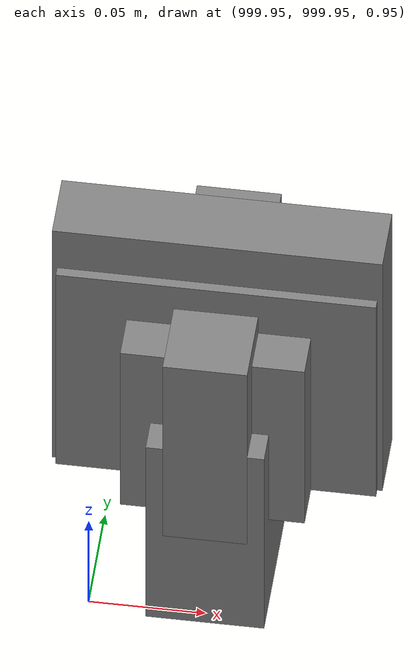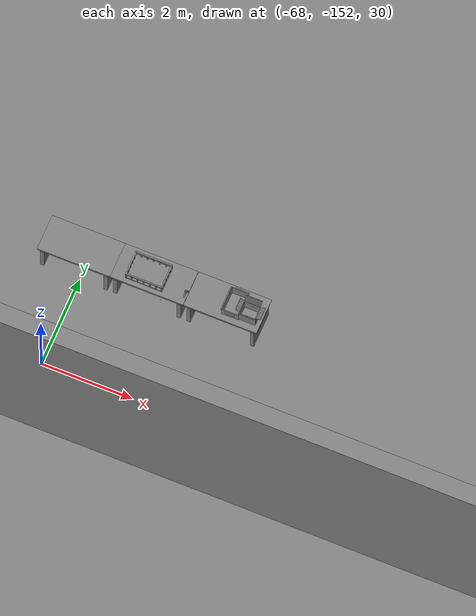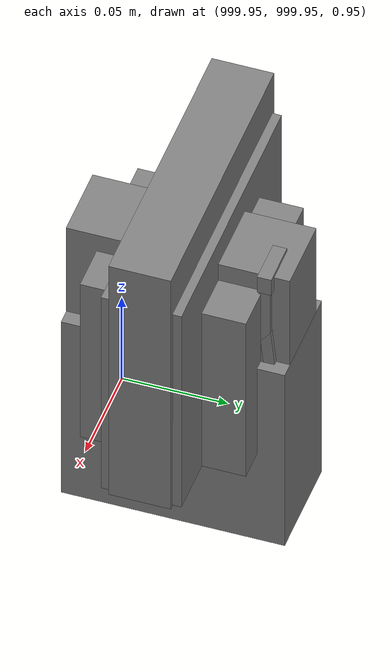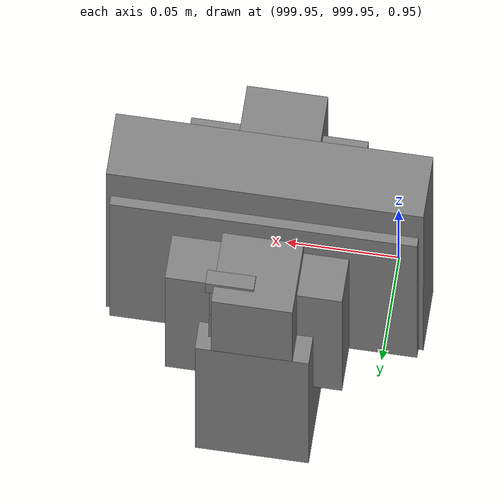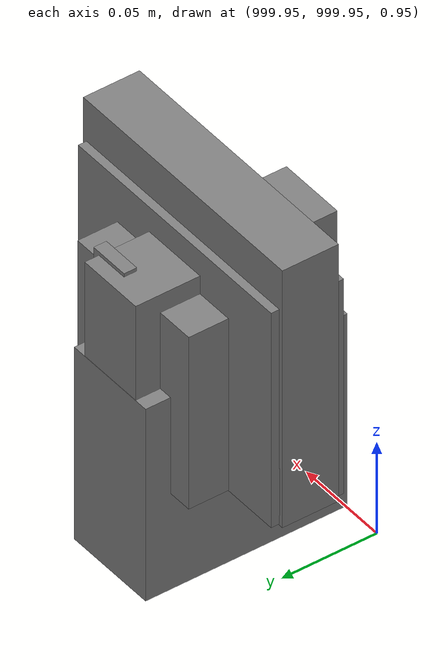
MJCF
<mujoco>
    <option gravity="0.000000000 0.000000000 -9.810000420" timestep="0.0049999999" integrator="implicitfast" density="1.225" viscosity="1.8000001e-05" noslip_iterations="10" iterations="100" sdf_iterations="50">
        <flag multiccd="disable"/>
    </option>
    <size memory="1000M"/>
    <compiler coordinate="local"/>
    <worldbody>
        <light cutoff="30" pos="0 1 1" dir="0 -1 -2"/>
        <light cutoff="30" pos="0 -1 1" dir="0 1 -2"/>
        <body pos="1000.000000000 1000.000000000 1.000000000" euler="0.000000000 0.000000000 180.000000000" name="openloong_gripper_2f85_fix_base_usda_battery_01">
            <geom contype="1" conaffinity="1" density="1000" type="box" material="" rgba="0.500000000 0.500000000 0.500000000 1.000000000" solimp="0.899999976 0.949999988 0.001000000" friction="1.000000000 0.005000000 0.000100000" solref="0.020000000 1.000000000" margin="0" condim="3" group="0" pos="-0.011123657 -0.041940309 0.101691343" quat="1.000000000 0.000000000 0.000000000 0.000000000" size="0.010800000 0.003375000 0.004725000" name="openloong_gripper_2f85_fix_base_usda_geom_5A3F01C7_A400_4B8D_A458_F4E76C8074EA"/>
            <geom contype="1" conaffinity="1" density="1000" type="box" material="" rgba="0.500000000 0.500000000 0.500000000 1.000000000" solimp="0.899999976 0.949999988 0.001000000" friction="1.000000000 0.005000000 0.000100000" solref="0.020000000 1.000000000" margin="0" condim="3" group="0" pos="-0.010876465 -0.044247437 0.047066893" quat="0.998702705 -0.050920475 0.000000000 0.000000000" size="0.009450001 0.002700000 0.024975000" name="openloong_gripper_2f85_fix_base_usda_geom_8A18FBBE_CB79_4FC0_815D_17788DCDB90C"/>
            <geom contype="1" conaffinity="1" density="1000" type="box" material="" rgba="0.500000000 0.500000000 0.500000000 1.000000000" solimp="0.899999976 0.949999988 0.001000000" friction="1.000000000 0.005000000 0.000100000" solref="0.020000000 1.000000000" margin="0" condim="3" group="0" pos="-0.001235962 -0.000659180 0.047381196" quat="1.000000000 0.000000000 0.000000000 0.000000000" size="0.039420001 0.039150000 0.047250003" name="openloong_gripper_2f85_fix_base_usda_geom_F8D5B451_3831_40A7_86F3_402BB22D2F56"/>
            <geom contype="1" conaffinity="1" density="1000" type="box" material="" rgba="0.500000000 0.500000000 0.500000000 1.000000000" solimp="0.899999976 0.949999988 0.001000000" friction="1.000000000 0.005000000 0.000100000" solref="0.020000000 1.000000000" margin="0" condim="3" group="0" pos="-0.010876465 -0.039138794 0.009851727" quat="1.000000000 0.000000000 0.000000000 0.000000000" size="0.009450001 0.010800000 0.013500000" name="openloong_gripper_2f85_fix_base_usda_geom_333269D5_940C_48BA_8E22_53324CBFCC62"/>
            <geom contype="1" conaffinity="1" density="1000" type="box" material="" rgba="0.500000000 0.500000000 0.500000000 1.000000000" solimp="0.899999976 0.949999988 0.001000000" friction="1.000000000 0.005000000 0.000100000" solref="0.020000000 1.000000000" margin="0" condim="3" group="0" pos="-0.010876465 -0.041528322 0.071508206" quat="1.000000000 0.000000000 0.000000000 0.000000000" size="0.009450001 0.002700000 0.027000001" name="openloong_gripper_2f85_fix_base_usda_geom_07A2FB65_44B0_4AFB_A2E7_A8F8ABB4F62F"/>
            <freejoint name="openloong_gripper_2f85_fix_base_usda_battery_01_joint"/>
            <site size="0.005000000 0.005000000 0.005000000" rgba="0.500000000 0.500000000 0.500000000 1.000000000" pos="0.000000000 0.000000000 0.000000000" quat="0.999961913 0.008726500 0.000000000 0.000000000" group="0" type="sphere" name="openloong_gripper_2f85_fix_base_usda_battery_01site"/>
        </body>
        <body pos="-65.899276733 -148.867401123 31.163518906" euler="-90.202194214 -52.040443420 15.125502586" mocap="true" name="spotlight3_SpotLight"/>
        <body pos="1000.000000000 1000.000000000 1.000000000" euler="0.000011953 0.000005123 -179.999984741" name="openloong_gripper_2f85_fix_base_usda_intel_box">
            <geom contype="1" conaffinity="1" density="1000" type="box" material="" rgba="0.500000000 0.500000000 0.500000000 1.000000000" solimp="0.899999976 0.949999988 0.001000000" friction="1.000000000 0.005000000 0.000100000" solref="0.020000000 1.000000000" margin="0" condim="3" group="0" pos="0.000000000 -0.000067139 0.000082284" quat="0.707106709 0.000000225 0.000000253 0.707106650" size="0.052800003 0.025300000 0.052800003" name="openloong_gripper_2f85_fix_base_usda_geom_404A122A_8F2E_4FF6_A87F_AAD72DCE11EC"/>
            <freejoint name="openloong_gripper_2f85_fix_base_usda_intel_box_joint"/>
            <site size="0.005000000 0.005000000 0.005000000" rgba="0.500000000 0.500000000 0.500000000 1.000000000" pos="0.000000000 0.000000000 0.000000000" quat="0.999961913 0.008726500 0.000000000 0.000000000" group="0" type="sphere" name="openloong_gripper_2f85_fix_base_usda_intel_boxsite"/>
        </body>
        <body pos="1000.000000000 1000.000000000 1.000000000" euler="0.000000000 0.000000000 180.000000000" name="openloong_gripper_2f85_fix_base_usda_cpu_fan">
            <geom contype="1" conaffinity="1" density="1000" type="box" material="" rgba="0.500000000 0.500000000 0.500000000 1.000000000" solimp="0.899999976 0.949999988 0.001000000" friction="1.000000000 0.005000000 0.000100000" solref="0.020000000 1.000000000" margin="0" condim="3" group="0" pos="0.000000000 0.000000000 0.070034981" quat="0.000000000 0.000000000 0.000000000 1.000000000" size="0.070700005 0.014699999 0.070700005" name="openloong_gripper_2f85_fix_base_usda_geom_6961328E_55CC_4CDD_A501_218A7D68B2D8"/>
            <freejoint name="openloong_gripper_2f85_fix_base_usda_cpu_fan_joint"/>
            <site size="0.005000000 0.005000000 0.005000000" rgba="0.500000000 0.500000000 0.500000000 1.000000000" pos="0.000000000 0.000000000 0.000000000" quat="0.999961913 0.008726535 0.000000000 0.000000000" group="0" type="sphere" name="openloong_gripper_2f85_fix_base_usda_cpu_fancsite"/>
        </body>
        <body pos="1000.000000000 1000.000000000 1.000000000" euler="0.000000000 0.000000000 180.000000000" name="openloong_gripper_2f85_fix_base_usda_wifi_box">
            <geom contype="1" conaffinity="1" density="1000" type="box" material="" rgba="0.500000000 0.500000000 0.500000000 1.000000000" solimp="0.899999976 0.949999988 0.001000000" friction="1.000000000 0.005000000 0.000100000" solref="0.020000000 1.000000000" margin="0" condim="3" group="0" pos="0.000000000 0.000000000 0.058978677" quat="0.000000000 0.000000047 0.000000000 1.000000000" size="0.068499997 0.018999999 0.059000000" name="openloong_gripper_2f85_fix_base_usda_geom_8ACF43A3_9B57_4AA2_9B56_E7149E546909"/>
            <freejoint name="openloong_gripper_2f85_fix_base_usda_wifi_box_joint"/>
            <site size="0.005000000 0.005000000 0.005000000" rgba="0.500000000 0.500000000 0.500000000 1.000000000" pos="0.000000000 0.000000000 0.000000000" quat="0.999961913 0.008726500 0.000000000 0.000000000" group="0" type="sphere" name="openloong_gripper_2f85_fix_base_usda_wifi_boxsite"/>
        </body>
        <body pos="1000.000000000 999.999938965 1.000000000" euler="0.000000000 0.000000000 180.000000000" name="openloong_gripper_2f85_fix_base_usda_intelcore_i5">
            <geom contype="1" conaffinity="1" density="1000" type="box" material="" rgba="0.500000000 0.500000000 0.500000000 1.000000000" solimp="0.899999976 0.949999988 0.001000000" friction="1.000000000 0.005000000 0.000100000" solref="0.020000000 1.000000000" margin="0" condim="3" group="0" pos="0.000000000 0.000000000 0.051722717" quat="0.707106709 0.000000000 0.000000000 -0.707106769" size="0.052800000 0.018080002 0.052800000" name="openloong_gripper_2f85_fix_base_usda_geom_258E2AFB_6566_4A82_97F0_317B87BA70BE"/>
            <freejoint name="openloong_gripper_2f85_fix_base_usda_intelcore_i5_joint"/>
            <site size="0.005000000 0.005000000 0.005000000" rgba="0.500000000 0.500000000 0.500000000 1.000000000" pos="0.000000000 0.000000000 0.000000000" quat="0.999961913 0.008726534 0.000000000 0.000000000" group="0" type="sphere" name="openloong_gripper_2f85_fix_base_usda_intelcore_i5site"/>
        </body>
        <body pos="-66.356681824 -149.530242920 31.165327072" euler="-117.509765625 -61.843044281 -101.470710754" mocap="true" name="spotlight2_SpotLight"/>
        <body pos="-66.018043518 -149.637756348 31.169094086" euler="122.672851562 -60.227375031 -47.035202026" mocap="true" name="spotlight1_SpotLight"/>
        <body pos="-64.866622925 -149.383972168 30.183746338" euler="89.999984741 89.999946594 0.000000000" name="openloong_gripper_2f85_fix_base_usda_bluebox_01">
            <geom contype="1" conaffinity="1" density="1000" type="box" material="" rgba="0.500000000 0.500000000 0.500000000 1.000000000" solimp="0.899999976 0.949999988 0.001000000" friction="1.000000000 0.005000000 0.000100000" solref="0.020000000 1.000000000" margin="0" condim="3" group="0" pos="0.276580811 0.187225342 0.000068665" quat="0.707106948 0.000077471 0.707106352 0.000077486" size="0.100000001 0.057999998 0.010000000" name="openloong_gripper_2f85_fix_base_usda_geom_110708A8_2FF9_488E_BF90_1206EE2F59D6"/>
            <geom contype="1" conaffinity="1" density="1000" type="box" material="" rgba="0.500000000 0.500000000 0.500000000 1.000000000" solimp="0.899999976 0.949999988 0.001000000" friction="1.000000000 0.005000000 0.000100000" solref="0.020000000 1.000000000" margin="0" condim="3" group="0" pos="0.000000000 0.002883911 0.000000000" quat="0.999999881 0.000000000 0.000000000 0.000000000" size="0.254000008 0.003000000 0.172000006" name="openloong_gripper_2f85_fix_base_usda_geom_DEA259A4_4F6D_4804_B9C9_D6946F0BED7A"/>
            <geom contype="1" conaffinity="1" density="1000" type="box" material="" rgba="0.500000000 0.500000000 0.500000000 1.000000000" solimp="0.899999976 0.949999988 0.001000000" friction="1.000000000 0.005000000 0.000100000" solref="0.020000000 1.000000000" margin="0" condim="3" group="0" pos="0.000000000 0.124874115 0.173484802" quat="0.999796331 0.020176515 -0.000000015 0.000000030" size="0.259999990 0.119999997 0.007000000" name="openloong_gripper_2f85_fix_base_usda_geom_D429D1DF_AC98_43B1_87E2_7A104F6D5BF6"/>
            <geom contype="1" conaffinity="1" density="1000" type="box" material="" rgba="0.500000000 0.500000000 0.500000000 1.000000000" solimp="0.899999976 0.949999988 0.001000000" friction="1.000000000 0.005000000 0.000100000" solref="0.020000000 1.000000000" margin="0" condim="3" group="0" pos="0.000000000 0.124874115 -0.173469543" quat="0.999796331 -0.020176545 -0.000000015 0.000000000" size="0.259999990 0.119999997 0.007000000" name="openloong_gripper_2f85_fix_base_usda_geom_5B33C397_C3B6_4607_B4E2_53D8AA26BA07"/>
            <geom contype="1" conaffinity="1" density="1000" type="box" material="" rgba="0.500000000 0.500000000 0.500000000 1.000000000" solimp="0.899999976 0.949999988 0.001000000" friction="1.000000000 0.005000000 0.000100000" solref="0.020000000 1.000000000" margin="0" condim="3" group="0" pos="0.000000000 0.214008331 0.188980103" quat="0.999912977 0.013176724 0.000000015 0.000000000" size="0.259999990 0.029999999 0.012500000" name="openloong_gripper_2f85_fix_base_usda_geom_2B1E435F_4E41_4DED_8243_8F713D371EFD"/>
            <geom contype="1" conaffinity="1" density="1000" type="box" material="" rgba="0.500000000 0.500000000 0.500000000 1.000000000" solimp="0.899999976 0.949999988 0.001000000" friction="1.000000000 0.005000000 0.000100000" solref="0.020000000 1.000000000" margin="0" condim="3" group="0" pos="-0.258361816 0.125289917 0.001876831" quat="0.702796936 -0.020792112 0.710783124 0.020769298" size="0.189999998 0.119999997 0.009000000" name="openloong_gripper_2f85_fix_base_usda_geom_768805E8_A735_4AC2_AC30_D78C8F2DD14B"/>
            <geom contype="1" conaffinity="1" density="1000" type="box" material="" rgba="0.500000000 0.500000000 0.500000000 1.000000000" solimp="0.899999976 0.949999988 0.001000000" friction="1.000000000 0.005000000 0.000100000" solref="0.020000000 1.000000000" margin="0" condim="3" group="0" pos="0.000000000 0.214008331 -0.188980103" quat="0.999912977 -0.013176769 0.000000030 0.000000015" size="0.259999990 0.029999999 0.012500000" name="openloong_gripper_2f85_fix_base_usda_geom_B85CCE67_332C_4AA1_8B27_25D51D77C081"/>
            <geom contype="1" conaffinity="1" density="1000" type="box" material="" rgba="0.500000000 0.500000000 0.500000000 1.000000000" solimp="0.899999976 0.949999988 0.001000000" friction="1.000000000 0.005000000 0.000100000" solref="0.020000000 1.000000000" margin="0" condim="3" group="0" pos="-0.276611328 0.187225342 0.000068665" quat="0.707106650 0.000077441 0.707106709 0.000077456" size="0.100000001 0.057999998 0.010000000" name="openloong_gripper_2f85_fix_base_usda_geom_1427C971_F806_4BBA_832F_C404AA1F860E"/>
            <geom contype="1" conaffinity="1" density="1000" type="box" material="" rgba="0.500000000 0.500000000 0.500000000 1.000000000" solimp="0.899999976 0.949999988 0.001000000" friction="1.000000000 0.005000000 0.000100000" solref="0.020000000 1.000000000" margin="0" condim="3" group="0" pos="0.258331299 0.125289917 0.001876831" quat="0.702851415 0.018856421 0.710823774 -0.019329369" size="0.189999998 0.119999997 0.009000000" name="openloong_gripper_2f85_fix_base_usda_geom_C4AC8D47_5616_4901_AB34_ED0504B45EAE"/>
            <freejoint name="openloong_gripper_2f85_fix_base_usda_bluebox_01_joint"/>
            <site size="0.005000000 0.005000000 0.005000000" rgba="0.500000000 0.500000000 0.500000000 1.000000000" pos="0.000000000 0.000000000 0.000000000" quat="0.999961913 0.008726534 0.000000000 0.000000000" group="0" type="sphere" name="openloong_gripper_2f85_fix_base_usda_bluebox_01site"/>
        </body>
        <body pos="-64.496299744 -149.491867065 30.235729218" euler="0.000000000 0.000000000 89.999946594" name="openloong_gripper_2f85_fix_base_usda_cardboardbox_01">
            <geom contype="1" conaffinity="1" density="1000" type="box" material="" rgba="0.500000000 0.500000000 0.500000000 1.000000000" solimp="0.899999976 0.949999988 0.001000000" friction="1.000000000 0.005000000 0.000100000" solref="0.020000000 1.000000000" margin="0" condim="3" group="0" pos="-0.003166199 -0.004086494 0.005052090" quat="1.000000000 0.000000000 0.000000000 0.000000000" size="0.142499998 0.177500010 0.005000000" name="openloong_gripper_2f85_fix_base_usda_geom_BCED3A6A_16F2_4115_8378_4F26E8CCCC2D"/>
            <geom contype="1" conaffinity="1" density="1000" type="box" material="" rgba="0.500000000 0.500000000 0.500000000 1.000000000" solimp="0.899999976 0.949999988 0.001000000" friction="1.000000000 0.005000000 0.000100000" solref="0.020000000 1.000000000" margin="0" condim="3" group="0" pos="-0.003166199 0.170316696 0.150570869" quat="1.000000000 0.000000000 0.000000000 0.000000000" size="0.142499998 0.005000000 0.149999991" name="openloong_gripper_2f85_fix_base_usda_geom_00997D1A_7537_4DD0_9683_C51D5866D406"/>
            <geom contype="1" conaffinity="1" density="1000" type="box" material="" rgba="0.500000000 0.500000000 0.500000000 1.000000000" solimp="0.899999976 0.949999988 0.001000000" friction="1.000000000 0.005000000 0.000100000" solref="0.020000000 1.000000000" margin="0" condim="3" group="0" pos="-0.147399902 -0.005307198 0.150570869" quat="1.000000000 0.000000000 0.000000000 0.000000000" size="0.005000000 0.177500010 0.149999991" name="openloong_gripper_2f85_fix_base_usda_geom_B5F8C559_BC66_420C_B794_CCB7388A86D5"/>
            <geom contype="1" conaffinity="1" density="1000" type="box" material="" rgba="0.500000000 0.500000000 0.500000000 1.000000000" solimp="0.899999976 0.949999988 0.001000000" friction="1.000000000 0.005000000 0.000100000" solref="0.020000000 1.000000000" margin="0" condim="3" group="0" pos="0.140275955 -0.005307198 0.150570869" quat="1.000000000 0.000000000 0.000000000 0.000000000" size="0.005000000 0.177500010 0.149999991" name="openloong_gripper_2f85_fix_base_usda_geom_CC597B13_224D_4D80_827B_903E25F95683"/>
            <geom contype="1" conaffinity="1" density="1000" type="box" material="" rgba="0.500000000 0.500000000 0.500000000 1.000000000" solimp="0.899999976 0.949999988 0.001000000" friction="1.000000000 0.005000000 0.000100000" solref="0.020000000 1.000000000" margin="0" condim="3" group="0" pos="-0.003166199 -0.181550980 0.150570869" quat="1.000000000 0.000000000 0.000000000 0.000000000" size="0.142499998 0.005000000 0.149999991" name="openloong_gripper_2f85_fix_base_usda_geom_39F770EB_017F_4A90_B3CD_2A1DBC5C0527"/>
            <freejoint name="openloong_gripper_2f85_fix_base_usda_cardboardbox_01_joint"/>
            <site size="0.005000000 0.005000000 0.005000000" rgba="0.500000000 0.500000000 0.500000000 1.000000000" pos="0.000000000 0.000000000 0.000000000" quat="0.999961913 0.008726535 0.000000000 0.000000000" group="0" type="sphere" name="openloong_gripper_2f85_fix_base_usda_site_68E7C7A6_871B_4E43_931A_53107CCD6C15"/>
            <body pos="0.139160156 -0.004048347 0.301930904" euler="-179.999954224 49.383502960 179.999954224" name="openloong_gripper_2f85_fix_base_usda_A1_006">
                <geom contype="1" conaffinity="1" density="1000" type="box" material="" rgba="0.500000000 0.500000000 0.500000000 1.000000000" solimp="0.899999976 0.949999988 0.001000000" friction="1.000000000 0.005000000 0.000100000" solref="0.020000000 1.000000000" margin="0" condim="3" group="0" pos="-0.071587563 0.000009537 0.001745224" quat="0.999999881 0.000000000 0.000000000 0.000000000" size="0.071249999 0.179999992 0.002500000" name="openloong_gripper_2f85_fix_base_usda_geom_768B79FF_C58E_4101_A864_F68B7A405FB3"/>
                <joint armature="0" stiffness="0.07" damping="0.0099999998" axis="0.000000 1.000000 0.000000" type="hinge" name="openloong_gripper_2f85_fix_base_usda_A1_006"/>
            </body>
            <body pos="-0.145902634 -0.004086494 0.301938057" euler="-180.000000000 -60.000011444 -180.000000000" name="openloong_gripper_2f85_fix_base_usda_A2_006">
                <geom contype="1" conaffinity="1" density="1000" type="box" material="" rgba="0.500000000 0.500000000 0.500000000 1.000000000" solimp="0.899999976 0.949999988 0.001000000" friction="1.000000000 0.005000000 0.000100000" solref="0.020000000 1.000000000" margin="0" condim="3" group="0" pos="0.071268082 0.000009537 0.002717972" quat="0.000002921 0.000000000 -0.000000030 0.999999881" size="0.071249999 0.179999992 0.002500000" name="openloong_gripper_2f85_fix_base_usda_geom_5F376D77_11FE_4F4D_8C74_65B4961EE131"/>
                <joint armature="0" stiffness="0.07" damping="0.0099999998" axis="0.000000 1.000000 0.000000" type="hinge" name="openloong_gripper_2f85_fix_base_usda_A2_006"/>
            </body>
            <body pos="-0.003385544 0.175991058 0.301930904" euler="-125.858116150 -0.000004561 0.000002331" name="openloong_gripper_2f85_fix_base_usda_B2_006">
                <geom contype="1" conaffinity="1" density="1000" type="box" material="" rgba="0.500000000 0.500000000 0.500000000 1.000000000" solimp="0.899999976 0.949999988 0.001000000" friction="1.000000000 0.005000000 0.000100000" solref="0.020000000 1.000000000" margin="0" condim="3" group="0" pos="0.000009537 -0.070939064 -0.002470016" quat="0.999614120 0.027776197 -0.000000015 0.000000030" size="0.137500003 0.064999998 0.005000000" name="openloong_gripper_2f85_fix_base_usda_geom_3E7CB124_980F_41C4_906B_3BE6A991D2BB"/>
                <joint armature="0" stiffness="0.07" damping="0.0099999998" axis="1.000000 0.000000 0.000000" type="hinge" name="openloong_gripper_2f85_fix_base_usda_B2_006"/>
            </body>
            <body pos="-0.003385544 -0.184140205 0.301938057" euler="147.805557251 0.000000000 0.000000000" name="openloong_gripper_2f85_fix_base_usda_B1_006">
                <geom contype="1" conaffinity="1" density="1000" type="box" material="" rgba="0.500000000 0.500000000 0.500000000 1.000000000" solimp="0.899999976 0.949999988 0.001000000" friction="1.000000000 0.005000000 0.000100000" solref="0.020000000 1.000000000" margin="0" condim="3" group="0" pos="-0.000028610 0.070202351 -0.002703667" quat="0.999614179 -0.027776167 0.000000000 0.000000000" size="0.137500003 0.064999998 0.005000000" name="openloong_gripper_2f85_fix_base_usda_geom_E9ABAF32_06D4_417C_BDA4_43E0D1FDBB09"/>
                <joint armature="0" stiffness="0.07" damping="0.0099999998" axis="1.000000 0.000000 0.000000" type="hinge" name="openloong_gripper_2f85_fix_base_usda_B1_006"/>
            </body>
        </body>
        <body pos="-65.882858276 -149.481979370 30.229999542" euler="-64.487716675 0.000000000 0.000000000" name="openloong_gripper_2f85_fix_base_usda_Barcode">
            <geom contype="1" conaffinity="1" density="1000" type="box" material="" rgba="0.500000000 0.500000000 0.500000000 1.000000000" solimp="0.899999976 0.949999988 0.001000000" friction="1.000000000 0.005000000 0.000100000" solref="0.020000000 1.000000000" margin="0" condim="3" group="0" pos="0.000000000 0.013038635 0.001419067" quat="0.000000000 0.000000000 0.000000000 1.000000119" size="0.034000002 0.010000000 0.017999999" name="openloong_gripper_2f85_fix_base_usda_geom_A003CFEB_4E90_4A49_B1CC_EB044BC65930"/>
            <geom contype="1" conaffinity="1" density="1000" type="box" material="" rgba="0.500000000 0.500000000 0.500000000 1.000000000" solimp="0.899999976 0.949999988 0.001000000" friction="1.000000000 0.005000000 0.000100000" solref="0.020000000 1.000000000" margin="0" condim="3" group="0" pos="0.000000000 -0.035301208 -0.007095337" quat="0.000000000 0.000000000 -0.043619365 0.999048233" size="0.028999999 0.010000000 0.020000000" name="openloong_gripper_2f85_fix_base_usda_geom_7901324C_59B5_4779_8112_819321010D00"/>
            <geom contype="1" conaffinity="1" density="1000" type="box" material="" rgba="0.500000000 0.500000000 0.500000000 1.000000000" solimp="0.899999976 0.949999988 0.001000000" friction="1.000000000 0.005000000 0.000100000" solref="0.020000000 1.000000000" margin="0" condim="3" group="0" pos="0.000000000 -0.043411255 -0.011749268" quat="0.922262907 0.386563420 0.000000000 0.000000000" size="0.026000001 0.010000000 0.020000000" name="openloong_gripper_2f85_fix_base_usda_geom_A13AA281_52E2_4E03_A85B_105587F9730C"/>
            <geom contype="1" conaffinity="1" density="1000" type="box" material="" rgba="0.500000000 0.500000000 0.500000000 1.000000000" solimp="0.899999976 0.949999988 0.001000000" friction="1.000000000 0.005000000 0.000100000" solref="0.020000000 1.000000000" margin="0" condim="3" group="0" pos="0.000000000 -0.016967773 -0.031860352" quat="0.000000000 0.000000000 0.000000000 1.000000119" size="0.008000000 0.010000000 0.013000000" name="openloong_gripper_2f85_fix_base_usda_geom_AB1037A2_16B2_4CBD_AEF6_BDE511081EBF"/>
            <geom contype="1" conaffinity="1" density="1000" type="box" material="" rgba="0.500000000 0.500000000 0.500000000 1.000000000" solimp="0.899999976 0.949999988 0.001000000" friction="1.000000000 0.005000000 0.000100000" solref="0.020000000 1.000000000" margin="0" condim="3" group="0" pos="0.000000000 -0.001869202 0.000312805" quat="0.953716993 0.300705761 0.000000000 0.000000000" size="0.032000002 0.010000000 0.018999999" name="openloong_gripper_2f85_fix_base_usda_geom_EAF32CA3_3DB9_424C_BC8F_1E50A1CF9497"/>
            <geom contype="1" conaffinity="1" density="1000" type="box" material="" rgba="0.500000000 0.500000000 0.500000000 1.000000000" solimp="0.899999976 0.949999988 0.001000000" friction="1.000000000 0.005000000 0.000100000" solref="0.020000000 1.000000000" margin="0" condim="3" group="0" pos="0.000000000 -0.019531250 -0.003173828" quat="0.953716993 0.300705761 0.000000000 0.000000000" size="0.030999999 0.010000000 0.020000000" name="openloong_gripper_2f85_fix_base_usda_geom_E12FC90A_5C26_4B38_9337_DE98C6BB2941"/>
            <geom contype="1" conaffinity="1" density="1000" type="box" material="" rgba="0.500000000 0.500000000 0.500000000 1.000000000" solimp="0.899999976 0.949999988 0.001000000" friction="1.000000000 0.005000000 0.000100000" solref="0.020000000 1.000000000" margin="0" condim="3" group="0" pos="0.000000000 -0.035301208 -0.007095337" quat="0.953716993 0.300705761 0.000000000 0.000000000" size="0.028999999 0.010000000 0.020000000" name="openloong_gripper_2f85_fix_base_usda_geom_D0E55CDD_42C2_4B9A_985B_ED22E3B0217A"/>
            <geom contype="1" conaffinity="1" density="1000" type="box" material="" rgba="0.500000000 0.500000000 0.500000000 1.000000000" solimp="0.899999976 0.949999988 0.001000000" friction="1.000000000 0.005000000 0.000100000" solref="0.020000000 1.000000000" margin="0" condim="3" group="0" pos="0.000000000 -0.042617798 -0.071121216" quat="0.000000000 0.000000000 0.000000000 1.000000119" size="0.013000000 0.021000000 0.059999999" name="openloong_gripper_2f85_fix_base_usda_geom_375C5B17_03C7_4F5D_AE68_EC293215A27B"/>
            <freejoint name="openloong_gripper_2f85_fix_base_usda_Barcode_joint"/>
            <site size="0.005000000 0.005000000 0.005000000" rgba="0.500000000 0.500000000 0.500000000 1.000000000" pos="0.000000000 0.000000000 0.000000000" quat="1.000000000 0.000000000 0.000000000 0.000000000" group="0" type="sphere" name="openloong_gripper_2f85_fix_base_usda_Barcode_site"/>
        </body>
        <body pos="-66.745018005 -149.392349243 30.184000015" euler="0.000000000 0.000000000 89.999946594" name="[22331355557195]_Basket_01">
            <geom contype="1" conaffinity="1" density="1000" type="box" material="" rgba="0.500000000 0.500000000 0.500000000 1.000000000" solimp="0.899999976 0.949999988 0.001000000" friction="1.000000000 0.005000000 0.000100000" solref="0.020000000 1.000000000" margin="0" condim="3" group="0" pos="-0.052425385 0.389207840 0.089787483" quat="0.707107008 0.000000000 0.000000000 0.707106411" size="0.014249999 0.014249999 0.059999999" name="[22331355557195]_geom_431B03CE_5A04_4F78_9168_D12E2BD4A276"/>
            <geom contype="1" conaffinity="1" density="1000" type="box" material="" rgba="0.500000000 0.500000000 0.500000000 1.000000000" solimp="0.899999976 0.949999988 0.001000000" friction="1.000000000 0.005000000 0.000100000" solref="0.020000000 1.000000000" margin="0" condim="3" group="0" pos="0.264015198 -0.133043289 0.089787483" quat="0.707107008 0.000000000 0.000000000 0.707106411" size="0.014249999 0.014249999 0.059999999" name="[22331355557195]_geom_1A3CB89D_52E6_440C_95B3_420F05E29404"/>
            <geom contype="1" conaffinity="1" density="1000" type="box" material="" rgba="0.500000000 0.500000000 0.500000000 1.000000000" solimp="0.899999976 0.949999988 0.001000000" friction="1.000000000 0.005000000 0.000100000" solref="0.020000000 1.000000000" margin="0" condim="3" group="0" pos="-0.264015198 -0.265548706 0.089793205" quat="0.707107008 0.000000000 0.000000000 0.707106411" size="0.014249999 0.014249999 0.059999999" name="[22331355557195]_geom_3F5499B3_B43C_4A4E_BD32_3A04D2BE1FA9"/>
            <geom contype="1" conaffinity="1" density="1000" type="box" material="" rgba="0.500000000 0.500000000 0.500000000 1.000000000" solimp="0.899999976 0.949999988 0.001000000" friction="1.000000000 0.005000000 0.000100000" solref="0.020000000 1.000000000" margin="0" condim="3" group="0" pos="-0.160263062 -0.389322281 0.089793205" quat="0.707107008 0.000000000 0.000000000 0.707106411" size="0.014249999 0.014249999 0.059999999" name="[22331355557195]_geom_7D395AF1_276D_4AA2_A537_279D3AAD0465"/>
            <geom contype="1" conaffinity="1" density="1000" type="box" material="" rgba="0.500000000 0.500000000 0.500000000 1.000000000" solimp="0.899999976 0.949999988 0.001000000" friction="1.000000000 0.005000000 0.000100000" solref="0.020000000 1.000000000" margin="0" condim="3" group="0" pos="0.162265778 -0.389322281 0.089787483" quat="0.707107008 0.000000000 0.000000000 0.707106411" size="0.014249999 0.014249999 0.059999999" name="[22331355557195]_geom_9262B155_2CE8_4390_97AD_BF690D689479"/>
            <geom contype="1" conaffinity="1" density="1000" type="box" material="" rgba="0.500000000 0.500000000 0.500000000 1.000000000" solimp="0.899999976 0.949999988 0.001000000" friction="1.000000000 0.005000000 0.000100000" solref="0.020000000 1.000000000" margin="0" condim="3" group="0" pos="0.264015198 0.389207840 0.089787483" quat="0.707107008 0.000000000 0.000000000 0.707106411" size="0.014249999 0.014249999 0.059999999" name="[22331355557195]_geom_BB37FCFC_6759_4A5C_9187_BBF76E789B9B"/>
            <geom contype="1" conaffinity="1" density="1000" type="box" material="" rgba="0.500000000 0.500000000 0.500000000 1.000000000" solimp="0.899999976 0.949999988 0.001000000" friction="1.000000000 0.005000000 0.000100000" solref="0.020000000 1.000000000" margin="0" condim="3" group="0" pos="-0.264015198 -0.133043289 0.089793205" quat="0.707107008 0.000000000 0.000000000 0.707106411" size="0.014249999 0.014249999 0.059999999" name="[22331355557195]_geom_93D7CF1C_D6D0_4E94_A774_6D0D67EA1C40"/>
            <geom contype="1" conaffinity="1" density="1000" type="box" material="" rgba="0.500000000 0.500000000 0.500000000 1.000000000" solimp="0.899999976 0.949999988 0.001000000" friction="1.000000000 0.005000000 0.000100000" solref="0.020000000 1.000000000" margin="0" condim="3" group="0" pos="-0.264026642 0.269256592 0.089793205" quat="0.707107008 0.000000000 0.000000000 0.707106411" size="0.014249999 0.014249999 0.059999999" name="[22331355557195]_geom_D877806D_4E32_4819_A090_B04832AFE694"/>
            <geom contype="1" conaffinity="1" density="1000" type="box" material="" rgba="0.500000000 0.500000000 0.500000000 1.000000000" solimp="0.899999976 0.949999988 0.001000000" friction="1.000000000 0.005000000 0.000100000" solref="0.020000000 1.000000000" margin="0" condim="3" group="0" pos="0.054462433 0.389207840 0.089787483" quat="0.707107008 0.000000000 0.000000000 0.707106411" size="0.014249999 0.014249999 0.059999999" name="[22331355557195]_geom_8803D843_A6DD_4C57_9111_3D23D7F2BB6A"/>
            <geom contype="1" conaffinity="1" density="1000" type="box" material="" rgba="0.500000000 0.500000000 0.500000000 1.000000000" solimp="0.899999976 0.949999988 0.001000000" friction="1.000000000 0.005000000 0.000100000" solref="0.020000000 1.000000000" margin="0" condim="3" group="0" pos="0.054462433 -0.389322281 0.089787483" quat="0.707107008 0.000000000 0.000000000 0.707106411" size="0.014249999 0.014249999 0.059999999" name="[22331355557195]_geom_E01D3066_6FAA_49F8_96E3_DCC23315BEC5"/>
            <geom contype="1" conaffinity="1" density="1000" type="box" material="" rgba="0.500000000 0.500000000 0.500000000 1.000000000" solimp="0.899999976 0.949999988 0.001000000" friction="1.000000000 0.005000000 0.000100000" solref="0.020000000 1.000000000" margin="0" condim="3" group="0" pos="0.264015198 0.269256592 0.089793205" quat="0.707107008 0.000000000 0.000000000 0.707106411" size="0.014249999 0.014249999 0.059999999" name="[22331355557195]_geom_99087CCC_F69C_4404_8EA7_DFFFD60493A1"/>
            <geom contype="1" conaffinity="1" density="1000" type="box" material="" rgba="0.500000000 0.500000000 0.500000000 1.000000000" solimp="0.899999976 0.949999988 0.001000000" friction="1.000000000 0.005000000 0.000100000" solref="0.020000000 1.000000000" margin="0" condim="3" group="0" pos="0.264015198 -0.389322281 0.089787483" quat="0.707107008 0.000000000 0.000000000 0.707106411" size="0.014249999 0.014249999 0.059999999" name="[22331355557195]_geom_84149D0A_4940_4E74_8BEC_A4736420793F"/>
            <geom contype="1" conaffinity="1" density="1000" type="box" material="" rgba="0.500000000 0.500000000 0.500000000 1.000000000" solimp="0.899999976 0.949999988 0.001000000" friction="1.000000000 0.005000000 0.000100000" solref="0.020000000 1.000000000" margin="0" condim="3" group="0" pos="0.000000000 0.000000000 0.015998840" quat="0.707107008 0.000000000 0.000000000 0.707106411" size="0.403499991 0.279000014 0.015750000" name="[22331355557195]_geom_7F6E77E2_E017_400E_9B24_7C076F1F1291"/>
            <geom contype="1" conaffinity="1" density="1000" type="box" material="" rgba="0.500000000 0.500000000 0.500000000 1.000000000" solimp="0.899999976 0.949999988 0.001000000" friction="1.000000000 0.005000000 0.000100000" solref="0.020000000 1.000000000" margin="0" condim="3" group="0" pos="0.000000000 -0.389476776 0.163619041" quat="0.707107008 0.000000000 0.000000000 0.707106411" size="0.015000000 0.277500004 0.015750000" name="[22331355557195]_geom_50B3F2B5_CFDA_4D12_9244_9D5F00FAF720"/>
            <geom contype="1" conaffinity="1" density="1000" type="box" material="" rgba="0.500000000 0.500000000 0.500000000 1.000000000" solimp="0.899999976 0.949999988 0.001000000" friction="1.000000000 0.005000000 0.000100000" solref="0.020000000 1.000000000" margin="0" condim="3" group="0" pos="0.162265778 0.389207840 0.089787483" quat="0.707107008 0.000000000 0.000000000 0.707106411" size="0.014249999 0.014249999 0.059999999" name="[22331355557195]_geom_6C27579E_BC95_46CA_A4F5_B829B64926A6"/>
            <geom contype="1" conaffinity="1" density="1000" type="box" material="" rgba="0.500000000 0.500000000 0.500000000 1.000000000" solimp="0.899999976 0.949999988 0.001000000" friction="1.000000000 0.005000000 0.000100000" solref="0.020000000 1.000000000" margin="0" condim="3" group="0" pos="0.000000000 0.389471054 0.163619041" quat="0.707107008 0.000000000 0.000000000 0.707106411" size="0.015000000 0.277500004 0.015750000" name="[22331355557195]_geom_54666328_7343_4C92_9FF7_07A3477534DD"/>
            <geom contype="1" conaffinity="1" density="1000" type="box" material="" rgba="0.500000000 0.500000000 0.500000000 1.000000000" solimp="0.899999976 0.949999988 0.001000000" friction="1.000000000 0.005000000 0.000100000" solref="0.020000000 1.000000000" margin="0" condim="3" group="0" pos="-0.263511658 0.000000000 0.163619041" quat="0.707107008 0.000000000 0.000000000 0.707106411" size="0.403499991 0.015000000 0.015750000" name="[22331355557195]_geom_2BA52E69_0BED_4CE4_962D_B7F47890CCE1"/>
            <geom contype="1" conaffinity="1" density="1000" type="box" material="" rgba="0.500000000 0.500000000 0.500000000 1.000000000" solimp="0.899999976 0.949999988 0.001000000" friction="1.000000000 0.005000000 0.000100000" solref="0.020000000 1.000000000" margin="0" condim="3" group="0" pos="-0.264015198 0.141334534 0.089793205" quat="0.707107008 0.000000000 0.000000000 0.707106411" size="0.014249999 0.014249999 0.059999999" name="[22331355557195]_geom_38243BE9_DC02_4173_991B_0A1ED94397FA"/>
            <geom contype="1" conaffinity="1" density="1000" type="box" material="" rgba="0.500000000 0.500000000 0.500000000 1.000000000" solimp="0.899999976 0.949999988 0.001000000" friction="1.000000000 0.005000000 0.000100000" solref="0.020000000 1.000000000" margin="0" condim="3" group="0" pos="0.264015198 -0.265548706 0.089787483" quat="0.707107008 0.000000000 0.000000000 0.707106411" size="0.014249999 0.014249999 0.059999999" name="[22331355557195]_geom_CEFA624C_6565_4026_A6F2_8E8F2D93614D"/>
            <geom contype="1" conaffinity="1" density="1000" type="box" material="" rgba="0.500000000 0.500000000 0.500000000 1.000000000" solimp="0.899999976 0.949999988 0.001000000" friction="1.000000000 0.005000000 0.000100000" solref="0.020000000 1.000000000" margin="0" condim="3" group="0" pos="-0.160263062 0.389207840 0.089787483" quat="0.707107008 0.000000000 0.000000000 0.707106411" size="0.014249999 0.014249999 0.059999999" name="[22331355557195]_geom_7B515637_19AA_46A4_8D5D_3CF50335C9CD"/>
            <geom contype="1" conaffinity="1" density="1000" type="box" material="" rgba="0.500000000 0.500000000 0.500000000 1.000000000" solimp="0.899999976 0.949999988 0.001000000" friction="1.000000000 0.005000000 0.000100000" solref="0.020000000 1.000000000" margin="0" condim="3" group="0" pos="-0.052425385 -0.389322281 0.089787483" quat="0.707107008 0.000000000 0.000000000 0.707106411" size="0.014249999 0.014249999 0.059999999" name="[22331355557195]_geom_BC39667F_FC18_483E_80F8_35758AEFA79B"/>
            <geom contype="1" conaffinity="1" density="1000" type="box" material="" rgba="0.500000000 0.500000000 0.500000000 1.000000000" solimp="0.899999976 0.949999988 0.001000000" friction="1.000000000 0.005000000 0.000100000" solref="0.020000000 1.000000000" margin="0" condim="3" group="0" pos="-0.264026642 -0.389322281 0.089793205" quat="0.707107008 0.000000000 0.000000000 0.707106411" size="0.014249999 0.014249999 0.059999999" name="[22331355557195]_geom_A0F9976E_154C_4DA9_8B74_28924C52C628"/>
            <geom contype="1" conaffinity="1" density="1000" type="box" material="" rgba="0.500000000 0.500000000 0.500000000 1.000000000" solimp="0.899999976 0.949999988 0.001000000" friction="1.000000000 0.005000000 0.000100000" solref="0.020000000 1.000000000" margin="0" condim="3" group="0" pos="0.264015198 0.141334534 0.089787483" quat="0.707107008 0.000000000 0.000000000 0.707106411" size="0.014249999 0.014249999 0.059999999" name="[22331355557195]_geom_8D7C7702_BA1E_4A1A_AAA8_94A4FA59ECE0"/>
            <geom contype="1" conaffinity="1" density="1000" type="box" material="" rgba="0.500000000 0.500000000 0.500000000 1.000000000" solimp="0.899999976 0.949999988 0.001000000" friction="1.000000000 0.005000000 0.000100000" solref="0.020000000 1.000000000" margin="0" condim="3" group="0" pos="-0.264015198 0.389207840 0.089793205" quat="0.707107008 0.000000000 0.000000000 0.707106411" size="0.014249999 0.014249999 0.059999999" name="[22331355557195]_geom_F4E3CDD5_2D14_4FCA_AE38_3AB0921D9821"/>
            <geom contype="1" conaffinity="1" density="1000" type="box" material="" rgba="0.500000000 0.500000000 0.500000000 1.000000000" solimp="0.899999976 0.949999988 0.001000000" friction="1.000000000 0.005000000 0.000100000" solref="0.020000000 1.000000000" margin="0" condim="3" group="0" pos="0.264015198 0.004480362 0.089787483" quat="0.707107008 0.000000000 0.000000000 0.707106411" size="0.014249999 0.014249999 0.059999999" name="[22331355557195]_geom_D5008AB9_D602_405F_BD3B_E98A96FB25D8"/>
            <geom contype="1" conaffinity="1" density="1000" type="box" material="" rgba="0.500000000 0.500000000 0.500000000 1.000000000" solimp="0.899999976 0.949999988 0.001000000" friction="1.000000000 0.005000000 0.000100000" solref="0.020000000 1.000000000" margin="0" condim="3" group="0" pos="0.263694763 -0.000011444 0.163619041" quat="0.707107008 0.000000000 0.000000000 0.707106411" size="0.403499991 0.015000000 0.015750000" name="[22331355557195]_geom_A5EEBD76_1884_4028_B566_04AADD700EDF"/>
            <geom contype="1" conaffinity="1" density="1000" type="box" material="" rgba="0.500000000 0.500000000 0.500000000 1.000000000" solimp="0.899999976 0.949999988 0.001000000" friction="1.000000000 0.005000000 0.000100000" solref="0.020000000 1.000000000" margin="0" condim="3" group="0" pos="-0.264015198 0.004480362 0.089793205" quat="0.707107008 0.000000000 0.000000000 0.707106411" size="0.014249999 0.014249999 0.059999999" name="[22331355557195]_geom_CA6A7B5F_F6F3_415D_BDCC_A1293EA7F490"/>
            <freejoint name="[22331355557195]_joint_87837152_DB26_4D90_9E5C_FF2391D2F674"/>
        </body>
        <body pos="0.000000000 0.000000000 0.000000000" euler="0.000000000 0.000000000 0.000000000" name="Static Objects_Static Objects">
            <geom contype="1" conaffinity="1" density="1000" type="box" material="" rgba="0.500000000 0.500000000 0.500000000 1.000000000" solimp="0.899999976 0.949999988 0.001000000" friction="1.000000000 0.005000000 0.000100000" solref="0.020000000 1.000000000" margin="0" condim="3" group="0" pos="-67.544113159 -149.365814209 29.727830887" quat="0.500000417 0.499999970 0.499999553 0.499999970" size="0.381000012 0.319999993 0.041000001" name="Static Objects_geom_C90F2759_D867_40E7_A243_C88511707C81"/>
            <geom contype="1" conaffinity="1" density="1000" type="box" material="" rgba="0.500000000 0.500000000 0.500000000 1.000000000" solimp="0.899999976 0.949999988 0.001000000" friction="1.000000000 0.005000000 0.000100000" solref="0.020000000 1.000000000" margin="0" condim="3" group="0" pos="-68.239501953 -149.365814209 30.086868286" quat="0.500000417 0.499999970 0.499999553 0.499999970" size="0.370999992 0.039500002 0.745000005" name="Static Objects_geom_65E6EA79_8AAA_4A8D_98A8_687626A0693F"/>
            <geom contype="1" conaffinity="1" density="1000" type="box" material="" rgba="0.500000000 0.500000000 0.500000000 1.000000000" solimp="0.899999976 0.949999988 0.001000000" friction="1.000000000 0.005000000 0.000100000" solref="0.020000000 1.000000000" margin="0" condim="3" group="0" pos="-68.239501953 -149.365814209 30.147235870" quat="0.500000417 0.499999970 0.499999553 0.499999970" size="0.400000006 0.022000000 0.800000012" name="Static Objects_geom_4CC1D15F_576A_4513_B7F9_8557D455D7A4"/>
            <geom contype="1" conaffinity="1" density="1000" type="box" material="" rgba="0.500000000 0.500000000 0.500000000 1.000000000" solimp="0.899999976 0.949999988 0.001000000" friction="1.000000000 0.005000000 0.000100000" solref="0.020000000 1.000000000" margin="0" condim="3" group="0" pos="-68.934890747 -149.365814209 29.727830887" quat="0.500000417 0.499999970 0.499999553 0.499999970" size="0.381000012 0.319999993 0.041000001" name="Static Objects_geom_019BAE7A_77D2_409E_94F8_EC10ED76C5E2"/>
            <geom contype="1" conaffinity="1" density="1000" type="box" material="" rgba="0.500000000 0.500000000 0.500000000 1.000000000" solimp="0.899999976 0.949999988 0.001000000" friction="1.000000000 0.005000000 0.000100000" solref="0.020000000 1.000000000" margin="0" condim="3" group="0" pos="-68.239501953 -149.365814209 29.561563492" quat="0.500000417 0.499999970 0.499999553 0.499999970" size="0.020000000 0.022000000 0.660000026" name="Static Objects_geom_F4978493_56CE_4247_8C6B_3952BAAEF4A5"/>
            <geom contype="1" conaffinity="1" density="1000" type="box" material="" rgba="0.500000000 0.500000000 0.500000000 1.000000000" solimp="0.899999976 0.949999988 0.001000000" friction="1.000000000 0.005000000 0.000100000" solref="0.020000000 1.000000000" margin="0" condim="3" group="0" pos="-65.945671082 -149.365814209 29.727830887" quat="0.500000417 0.499999970 0.499999553 0.499999970" size="0.381000012 0.319999993 0.041000001" name="Static Objects_geom_8D3F8554_9D07_48B2_8182_FBD3154492FD"/>
            <geom contype="1" conaffinity="1" density="1000" type="box" material="" rgba="0.500000000 0.500000000 0.500000000 1.000000000" solimp="0.899999976 0.949999988 0.001000000" friction="1.000000000 0.005000000 0.000100000" solref="0.020000000 1.000000000" margin="0" condim="3" group="0" pos="-66.641059875 -149.365814209 30.086868286" quat="0.500000417 0.499999970 0.499999553 0.499999970" size="0.370999992 0.039500002 0.745000005" name="Static Objects_geom_0BD2BCFC_73F6_4F3D_B046_B86F251ECB34"/>
            <geom contype="1" conaffinity="1" density="1000" type="box" material="" rgba="0.500000000 0.500000000 0.500000000 1.000000000" solimp="0.899999976 0.949999988 0.001000000" friction="1.000000000 0.005000000 0.000100000" solref="0.020000000 1.000000000" margin="0" condim="3" group="0" pos="-66.641059875 -149.365814209 30.147235870" quat="0.500000417 0.499999970 0.499999553 0.499999970" size="0.400000006 0.022000000 0.800000012" name="Static Objects_geom_D310F07C_77F5_42B6_848E_ECC63CE99F46"/>
            <geom contype="1" conaffinity="1" density="1000" type="box" material="" rgba="0.500000000 0.500000000 0.500000000 1.000000000" solimp="0.899999976 0.949999988 0.001000000" friction="1.000000000 0.005000000 0.000100000" solref="0.020000000 1.000000000" margin="0" condim="3" group="0" pos="-67.336448669 -149.365814209 29.727830887" quat="0.500000417 0.499999970 0.499999553 0.499999970" size="0.381000012 0.319999993 0.041000001" name="Static Objects_geom_99801866_C837_41CD_BCAB_0B9EEE2EDB34"/>
            <geom contype="1" conaffinity="1" density="1000" type="box" material="" rgba="0.500000000 0.500000000 0.500000000 1.000000000" solimp="0.899999976 0.949999988 0.001000000" friction="1.000000000 0.005000000 0.000100000" solref="0.020000000 1.000000000" margin="0" condim="3" group="0" pos="-66.641059875 -149.365814209 29.561563492" quat="0.500000417 0.499999970 0.499999553 0.499999970" size="0.020000000 0.022000000 0.660000026" name="Static Objects_geom_FEF35704_804D_4218_80C3_B92D24F25DCC"/>
            <geom contype="1" conaffinity="1" density="1000" type="box" material="" rgba="0.500000000 0.500000000 0.500000000 1.000000000" solimp="0.899999976 0.949999988 0.001000000" friction="1.000000000 0.005000000 0.000100000" solref="0.020000000 1.000000000" margin="0" condim="3" group="0" pos="-64.338577271 -149.365814209 29.727830887" quat="0.500000417 0.499999970 0.499999553 0.499999970" size="0.381000012 0.319999993 0.041000001" name="Static Objects_geom_BF9D3767_9F16_42F3_8988_D83B8C664156"/>
            <geom contype="1" conaffinity="1" density="1000" type="box" material="" rgba="0.500000000 0.500000000 0.500000000 1.000000000" solimp="0.899999976 0.949999988 0.001000000" friction="1.000000000 0.005000000 0.000100000" solref="0.020000000 1.000000000" margin="0" condim="3" group="0" pos="-65.033966064 -149.365814209 30.086868286" quat="0.500000417 0.499999970 0.499999553 0.499999970" size="0.370999992 0.039500002 0.745000005" name="Static Objects_geom_2D57EAD7_2F70_43F7_B7A9_BBD4CA77AD87"/>
            <geom contype="1" conaffinity="1" density="1000" type="box" material="" rgba="0.500000000 0.500000000 0.500000000 1.000000000" solimp="0.899999976 0.949999988 0.001000000" friction="1.000000000 0.005000000 0.000100000" solref="0.020000000 1.000000000" margin="0" condim="3" group="0" pos="-65.033966064 -149.365814209 30.147235870" quat="0.500000417 0.499999970 0.499999553 0.499999970" size="0.400000006 0.022000000 0.800000012" name="Static Objects_geom_70389B67_5F4E_43FB_AF2F_54B2F23BE254"/>
            <geom contype="1" conaffinity="1" density="1000" type="box" material="" rgba="0.500000000 0.500000000 0.500000000 1.000000000" solimp="0.899999976 0.949999988 0.001000000" friction="1.000000000 0.005000000 0.000100000" solref="0.020000000 1.000000000" margin="0" condim="3" group="0" pos="-65.729354858 -149.365814209 29.727830887" quat="0.500000417 0.499999970 0.499999553 0.499999970" size="0.381000012 0.319999993 0.041000001" name="Static Objects_geom_5067AA23_2602_474D_820C_B8AAC3046DAF"/>
            <geom contype="1" conaffinity="1" density="1000" type="box" material="" rgba="0.500000000 0.500000000 0.500000000 1.000000000" solimp="0.899999976 0.949999988 0.001000000" friction="1.000000000 0.005000000 0.000100000" solref="0.020000000 1.000000000" margin="0" condim="3" group="0" pos="-65.033966064 -149.365814209 29.561563492" quat="0.500000417 0.499999970 0.499999553 0.499999970" size="0.020000000 0.022000000 0.660000026" name="Static Objects_geom_F990142C_7B1D_4173_A44E_4820C56F69F7"/>
            <geom contype="1" conaffinity="1" density="1000" type="box" material="" rgba="0.500000000 0.500000000 0.500000000 1.000000000" solimp="0.899999976 0.949999988 0.001000000" friction="1.000000000 0.005000000 0.000100000" solref="0.020000000 1.000000000" margin="0" condim="3" group="0" pos="-61.754566193 -137.853729248 33.906845093" quat="0.707107067 0.000000000 0.000000000 0.707106471" size="0.759999990 0.759999990 4.500000000" name="Static Objects_geom_E3484F73_303C_4DD5_8FC8_1582B69A5E0A"/>
            <geom contype="1" conaffinity="1" density="1000" type="box" material="" rgba="0.500000000 0.500000000 0.500000000 1.000000000" solimp="0.899999976 0.949999988 0.001000000" friction="1.000000000 0.005000000 0.000100000" solref="0.020000000 1.000000000" margin="0" condim="3" group="0" pos="-57.511135101 -144.927108765 31.707921982" quat="1.000000000 0.000000000 0.000000000 0.000000000" size="0.200000003 8.000000000 2.299999952" name="Static Objects_geom_6B63DFE9_113B_4903_BE23_2E97A876145B"/>
            <geom contype="1" conaffinity="1" density="1000" type="box" material="" rgba="0.500000000 0.500000000 0.500000000 1.000000000" solimp="0.899999976 0.949999988 0.001000000" friction="1.000000000 0.005000000 0.000100000" solref="0.020000000 1.000000000" margin="0" condim="3" group="0" pos="-80.517646790 -157.574050903 31.688196182" quat="0.707107067 0.000000000 0.000000000 0.707106471" size="0.600000024 0.600000024 2.299999952" name="Static Objects_geom_7FA94FBE_D6F7_4CDE_B9FC_36E5135F7AA7"/>
            <geom contype="1" conaffinity="1" density="1000" type="box" material="" rgba="0.500000000 0.500000000 0.500000000 1.000000000" solimp="0.899999976 0.949999988 0.001000000" friction="1.000000000 0.005000000 0.000100000" solref="0.020000000 1.000000000" margin="0" condim="3" group="0" pos="-80.711044312 -147.414932251 31.666158676" quat="1.000000000 0.000000000 0.000000000 0.000000000" size="0.200000003 10.000000000 2.299999952" name="Static Objects_geom_FB8E33D2_C2CD_4589_A92A_12F20B39CBD1"/>
            <geom contype="1" conaffinity="1" density="1000" type="box" material="" rgba="0.500000000 0.500000000 0.500000000 1.000000000" solimp="0.899999976 0.949999988 0.001000000" friction="1.000000000 0.005000000 0.000100000" solref="0.020000000 1.000000000" margin="0" condim="3" group="0" pos="-57.687217712 -137.434692383 31.688196182" quat="0.707107067 0.000000000 0.000000000 0.707106471" size="0.600000024 0.600000024 2.299999952" name="Static Objects_geom_41324922_3C63_47C8_A951_CBB588944677"/>
            <geom contype="1" conaffinity="1" density="1000" type="box" material="" rgba="0.500000000 0.500000000 0.500000000 1.000000000" solimp="0.899999976 0.949999988 0.001000000" friction="1.000000000 0.005000000 0.000100000" solref="0.020000000 1.000000000" margin="0" condim="3" group="0" pos="-69.537033081 -140.263229370 31.714921951" quat="0.707107067 0.000000000 0.000000000 0.707106471" size="0.759999990 4.500000000 2.299999952" name="Static Objects_geom_D472F179_BA2D_4FBE_80C0_B881A395EF67"/>
            <geom contype="1" conaffinity="1" density="1000" type="box" material="" rgba="0.500000000 0.500000000 0.500000000 1.000000000" solimp="0.899999976 0.949999988 0.001000000" friction="1.000000000 0.005000000 0.000100000" solref="0.020000000 1.000000000" margin="0" condim="3" group="0" pos="-80.073638916 -137.853713989 33.906845093" quat="0.707107067 0.000000000 0.000000000 0.707106471" size="0.759999990 0.759999990 4.500000000" name="Static Objects_geom_8558DDAB_C823_4922_8818_5EBF209E53C1"/>
            <geom contype="1" conaffinity="1" density="1000" type="box" material="" rgba="0.500000000 0.500000000 0.500000000 1.000000000" solimp="0.899999976 0.949999988 0.001000000" friction="1.000000000 0.005000000 0.000100000" solref="0.020000000 1.000000000" margin="0" condim="3" group="0" pos="-73.406707764 -155.734664917 31.707921982" quat="1.000000000 0.000000000 0.000000000 0.000000000" size="0.200000003 3.000000000 2.299999952" name="Static Objects_geom_49596FF4_8BCA_4C3D_B1C2_6C9ECBF13E63"/>
            <geom contype="1" conaffinity="1" density="1000" type="box" material="" rgba="0.500000000 0.500000000 0.500000000 1.000000000" solimp="0.899999976 0.949999988 0.001000000" friction="1.000000000 0.005000000 0.000100000" solref="0.020000000 1.000000000" margin="0" condim="3" group="0" pos="-68.497543335 -137.448257446 31.707921982" quat="0.707107067 0.000000000 0.000000000 0.707106471" size="0.200000003 14.000000000 2.299999952" name="Static Objects_geom_DFA9EA85_7EE1_49C0_8641_299E252C5DC4"/>
            <geom contype="1" conaffinity="1" density="1000" type="cylinder" material="" rgba="0.500000000 0.500000000 0.500000000 1.000000000" solimp="0.899999976 0.949999988 0.001000000" friction="1.000000000 0.005000000 0.000100000" solref="0.020000000 1.000000000" margin="0" condim="3" group="0" pos="-68.868522644 -142.134506226 31.711090088" quat="0.707107067 0.000000000 0.000000000 0.707106471" size="0.509999990 2.299999952 1.000000000" name="Static Objects_geom_FE4F6138_1883_4648_8F6B_34F933BE0716"/>
            <geom contype="1" conaffinity="1" density="1000" type="plane" material="" rgba="0.500000000 0.500000000 0.500000000 1.000000000" solimp="0.899999976 0.949999988 0.001000000" friction="1.000000000 0.005000000 0.000100000" solref="0.020000000 1.000000000" margin="0" condim="3" group="0" pos="-72.873703003 -147.131927490 29.409669876" quat="1.000000000 0.000000000 0.000000000 0.000000000" size="18.000000000 14.000000000 1.000000000" name="Static Objects_geom_7BF44E90_E630_4AFA_97D0_27764E4EB8D5"/>
            <geom contype="1" conaffinity="1" density="1000" type="box" material="" rgba="0.500000000 0.500000000 0.500000000 1.000000000" solimp="0.899999976 0.949999988 0.001000000" friction="1.000000000 0.005000000 0.000100000" solref="0.020000000 1.000000000" margin="0" condim="3" group="0" pos="-79.943580627 -157.782272339 31.707921982" quat="0.707107067 0.000000000 0.000000000 0.707106471" size="0.200000003 7.000000000 2.299999952" name="Static Objects_geom_3C91258A_7403_412C_A076_05967CC7C0A7"/>
            <geom contype="1" conaffinity="1" density="1000" type="box" material="" rgba="0.500000000 0.500000000 0.500000000 1.000000000" solimp="0.899999976 0.949999988 0.001000000" friction="1.000000000 0.005000000 0.000100000" solref="0.020000000 1.000000000" margin="0" condim="3" group="0" pos="-65.421028137 -152.903442383 31.707921982" quat="0.707107067 0.000000000 0.000000000 0.707106471" size="0.200000003 7.800000191 2.299999952" name="Static Objects_geom_01773E05_7EA8_46DA_B34D_138944E9080F"/>
            <geom contype="1" conaffinity="1" density="1000" type="box" material="" rgba="0.500000000 0.500000000 0.500000000 1.000000000" solimp="0.899999976 0.949999988 0.001000000" friction="1.000000000 0.005000000 0.000100000" solref="0.020000000 1.000000000" margin="0" condim="3" group="0" pos="-74.776908875 -149.964416504 31.688196182" quat="1.000000000 0.000000000 0.000000000 0.000000000" size="0.600000024 0.409999996 2.299999952" name="Static Objects_geom_CC10B904_C379_4634_940F_45BDF3CB1F64"/>
            <geom contype="1" conaffinity="1" density="1000" type="cylinder" material="" rgba="0.500000000 0.500000000 0.500000000 1.000000000" solimp="0.899999976 0.949999988 0.001000000" friction="1.000000000 0.005000000 0.000100000" solref="0.020000000 1.000000000" margin="0" condim="3" group="0" pos="-60.161884308 -142.134506226 31.711090088" quat="0.707107067 0.000000000 0.000000000 0.707106471" size="0.509999990 2.299999952 1.000000000" name="Static Objects_geom_4E78AFC0_5172_4A49_BB50_41DAB51BCC89"/>
            <geom contype="1" conaffinity="1" density="1000" type="cylinder" material="" rgba="0.500000000 0.500000000 0.500000000 1.000000000" solimp="0.899999976 0.949999988 0.001000000" friction="1.000000000 0.005000000 0.000100000" solref="0.020000000 1.000000000" margin="0" condim="3" group="0" pos="-75.382453918 -149.963455200 31.711090088" quat="0.707107067 0.000000000 0.000000000 0.707106471" size="0.409999996 2.299999952 1.000000000" name="Static Objects_geom_8E94CE34_39CA_4CB7_A43F_9324760FD923"/>
            <geom contype="1" conaffinity="1" density="1000" type="cylinder" material="" rgba="0.500000000 0.500000000 0.500000000 1.000000000" solimp="0.899999976 0.949999988 0.001000000" friction="1.000000000 0.005000000 0.000100000" solref="0.020000000 1.000000000" margin="0" condim="3" group="0" pos="-74.154960632 -149.963455200 31.711090088" quat="0.707107067 0.000000000 0.000000000 0.707106471" size="0.409999996 2.299999952 1.000000000" name="Static Objects_geom_D4972C4C_B34A_4115_B91D_744A90C18FC2"/>
            <geom contype="1" conaffinity="1" density="1000" type="cylinder" material="" rgba="0.500000000 0.500000000 0.500000000 1.000000000" solimp="0.899999976 0.949999988 0.001000000" friction="1.000000000 0.005000000 0.000100000" solref="0.020000000 1.000000000" margin="0" condim="3" group="0" pos="-77.566612244 -142.134506226 31.711090088" quat="0.707107067 0.000000000 0.000000000 0.707106471" size="0.509999990 2.299999952 1.000000000" name="Static Objects_geom_F3AE277F_90A6_4E13_AA64_A28EFF4153FE"/>
        </body>
        <body pos="-66.291030884 -149.869689941 29.018842697" euler="0.000000000 0.000000000 89.999946594" mocap="true" name="openloong_gripper_2f85_fix_base_usda_leftHandMocap"/>
        <body pos="-66.291030884 -149.869689941 29.018842697" euler="0.000000000 0.000000000 89.999946594" mocap="true" name="openloong_gripper_2f85_fix_base_usda_rightHandMocap"/>
        <body pos="-66.291030884 -149.869689941 30.218843460" euler="0.000000000 0.000000000 89.999946594" name="openloong_gripper_2f85_fix_base_usda_base_link">
            <geom contype="1" conaffinity="1" density="1000" type="mesh" material="" rgba="0.783999979 0.783999979 0.783999979 1.000000000" solimp="0.899999976 0.949999988 0.001000000" friction="1.000000000 0.005000000 0.000100000" solref="0.020000000 1.000000000" margin="0" condim="3" group="3" mesh="base_link" pos="0.000000000 0.000000000 0.000000000" quat="1.000000000 0.000000000 0.000000000 0.000000000" size="1.000000000 1.000000000 1.000000000" name="openloong_gripper_2f85_fix_base_usda__geom_7_2ECD5013_086E_4105_8297_7BB9BD8210C1"/>
            <site size="0.005000000 0.005000000 0.005000000" rgba="0.500000000 0.500000000 0.500000000 1.000000000" pos="0.000000000 0.000000000 0.000000000" quat="1.000000000 0.000000000 0.000000000 0.000000000" group="0" type="sphere" name="openloong_gripper_2f85_fix_base_usda_imu"/>
            <inertial mass="22.447001" pos="-0.005664100 -0.001336700 0.238289997" diaginertia="0.374352545 0.277180195 0.220617250" quat="0.999247074 0.035235517 -0.015086859 0.006023135"/>
            <body pos="0.000000000 0.000000000 0.299997330" euler="0.000000000 0.000000000 0.000000000" name="openloong_gripper_2f85_fix_base_usda_dummy_body">
                <geom contype="1" conaffinity="1" density="1000" type="sphere" material="" rgba="0.783999979 0.783999979 0.783999979 1.000000000" solimp="0.899999976 0.949999988 0.001000000" friction="1.000000000 0.005000000 0.000100000" solref="0.020000000 1.000000000" margin="0" condim="3" group="3" pos="0.000000000 0.000000000 0.000000000" quat="1.000000000 0.000000000 0.000000000 0.000000000" size="0.010000000 0.000000000 0.000000000" name="openloong_gripper_2f85_fix_base_usda__geom_8_25053A89_6BF1_4B90_9296_C921B137BEF1"/>
                <joint armature="0.0099999998" stiffness="0" damping="0.1" axis="0.000000 0.000000 1.000000" type="hinge" name="openloong_gripper_2f85_fix_base_usda_dummy_joint"/>
                <site size="0.010000000 0.005000000 0.005000000" rgba="0.500000000 0.500000000 0.500000000 1.000000000" pos="0.000000000 0.000000000 0.000000000" quat="1.000000000 0.000000000 0.000000000 0.000000000" group="3" type="sphere" name="openloong_gripper_2f85_fix_base_usda_dummy_site"/>
            </body>
            <body pos="0.009002686 0.000000000 0.406400681" euler="0.000000000 0.000000000 0.000000000" name="openloong_gripper_2f85_fix_base_usda_Link_head_yaw">
                <geom contype="1" conaffinity="1" density="1000" type="mesh" material="" rgba="0.783999979 0.783999979 0.783999979 1.000000000" solimp="0.899999976 0.949999988 0.001000000" friction="1.000000000 0.005000000 0.000100000" solref="0.020000000 1.000000000" margin="0" condim="3" group="3" mesh="Link_head_yaw" pos="0.000000000 0.000000000 0.000000000" quat="1.000000000 0.000000000 0.000000000 0.000000000" size="1.000000000 1.000000000 1.000000000" name="openloong_gripper_2f85_fix_base_usda__geom_10_9DF106F5_CBCC_4754_9052_1C019464AA2A"/>
                <inertial mass="0.84249002" pos="0.000000000 -0.002081400 0.044801001" diaginertia="0.000700588 0.000629000 0.000553812" quat="0.706933022 -0.015675601 0.015677100 0.706933022"/>
                <body pos="0.000000000 -0.034599304 0.048500061" euler="0.000000000 0.000000000 0.000000000" name="openloong_gripper_2f85_fix_base_usda_Link_head_pitch">
                    <geom contype="1" conaffinity="1" density="1000" type="mesh" material="" rgba="0.783999979 0.783999979 0.783999979 1.000000000" solimp="0.899999976 0.949999988 0.001000000" friction="1.000000000 0.005000000 0.000100000" solref="0.020000000 1.000000000" margin="0" condim="3" group="3" mesh="Link_head_pitch" pos="0.000000000 0.000000000 0.000000000" quat="1.000000000 0.000000000 0.000000000 0.000000000" size="1.000000000 1.000000000 1.000000000" name="openloong_gripper_2f85_fix_base_usda__geom_12_362B7050_85AE_43FB_B67D_6739A2616122"/>
                    <inertial mass="1.3943" pos="0.020569000 0.033004001 0.125000000" diaginertia="0.006381400 0.006289940 0.004481460" quat="0.973390222 0.008406822 0.228157058 0.019624906"/>
                    <body pos="0.000000000 0.029998779 0.000000000" euler="0.000000000 0.000000000 0.000000000" name="openloong_gripper_2f85_fix_base_usda_neck_center_body">
                        <site size="0.010000000 0.005000000 0.005000000" rgba="0.500000000 0.500000000 0.500000000 1.000000000" pos="0.000000000 0.000000000 0.000000000" quat="1.000000000 0.000000000 0.000000000 0.000000000" group="3" type="sphere" name="openloong_gripper_2f85_fix_base_usda_neck_center_site"/>
                        <body pos="0.020004272 0.000000000 0.149999619" euler="-0.000002229 39.998176575 -90.000205994" name="openloong_gripper_2f85_fix_base_usda_camera_head">
                            <site size="0.010000000 0.005000000 0.005000000" rgba="0.500000000 0.500000000 0.500000000 1.000000000" pos="0.000000000 0.000000000 0.000000000" quat="1.000000000 0.000000000 0.000000000 0.000000000" group="3" type="sphere" name="openloong_gripper_2f85_fix_base_usda_camera_head_site"/>
                        </body>
                    </body>
                </body>
            </body>
            <body pos="0.003997803 -0.161598206 0.392200470" euler="0.000000000 0.000000000 0.000000000" name="openloong_gripper_2f85_fix_base_usda_Link_arm_r_01">
                <geom contype="1" conaffinity="1" density="1000" type="mesh" material="" rgba="0.783999979 0.783999979 0.783999979 1.000000000" solimp="0.899999976 0.949999988 0.001000000" friction="1.000000000 0.005000000 0.000100000" solref="0.020000000 1.000000000" margin="0" condim="3" group="3" mesh="Link_arm_r_01" pos="0.000000000 0.000000000 0.000000000" quat="1.000000000 0.000000000 0.000000000 0.000000000" size="1.000000000 1.000000000 1.000000000" name="openloong_gripper_2f85_fix_base_usda__geom_14_BC85844A_96D6_4EBB_8919_70D4047E2EB1"/>
                <joint armature="0.0099999998" stiffness="0" damping="1" axis="0.000000 -1.000000 0.000000" limited="true" range="-170.000015259 170.000015259" type="hinge" name="openloong_gripper_2f85_fix_base_usda_J_arm_r_01"/>
                <inertial mass="0.75641" pos="0.004494600 -0.038293999 -0.000001874" diaginertia="0.000842990 0.000803050 0.000587120" quat="-0.000163502 0.707098067 0.000812463 0.707115054"/>
                <body pos="-0.041992188 -0.041000366 0.000000000" euler="0.000000000 0.000000000 0.000000000" name="openloong_gripper_2f85_fix_base_usda_Link_arm_r_02">
                    <geom contype="1" conaffinity="1" density="1000" type="mesh" material="" rgba="0.783999979 0.783999979 0.783999979 1.000000000" solimp="0.899999976 0.949999988 0.001000000" friction="1.000000000 0.005000000 0.000100000" solref="0.020000000 1.000000000" margin="0" condim="3" group="3" mesh="Link_arm_r_02" pos="0.000000000 0.000000000 0.000000000" quat="1.000000000 0.000000000 0.000000000 0.000000000" size="1.000000000 1.000000000 1.000000000" name="openloong_gripper_2f85_fix_base_usda__geom_16_30EE73E3_4A19_421C_B51D_52E5BD914B7D"/>
                    <joint armature="0.0099999998" stiffness="0" damping="1" axis="-1.000000 0.000000 0.000000" limited="true" range="-105.000244141 105.000244141" type="hinge" name="openloong_gripper_2f85_fix_base_usda_J_arm_r_02"/>
                    <inertial mass="0.98500001" pos="0.041999999 -0.067430697 0.000000000" diaginertia="0.002262690 0.001730990 0.001154020" quat="0.500000000 0.500000000 -0.500000000 0.500000000"/>
                    <body pos="0.041992188 -0.122596741 0.000000000" euler="0.000000000 0.000000000 0.000000000" name="openloong_gripper_2f85_fix_base_usda_Link_arm_r_03">
                        <geom contype="1" conaffinity="1" density="1000" type="mesh" material="" rgba="0.783999979 0.783999979 0.783999979 1.000000000" solimp="0.899999976 0.949999988 0.001000000" friction="1.000000000 0.005000000 0.000100000" solref="0.020000000 1.000000000" margin="0" condim="3" group="3" mesh="Link_arm_r_03" pos="0.000000000 0.000000000 0.000000000" quat="1.000000000 0.000000000 0.000000000 0.000000000" size="1.000000000 1.000000000 1.000000000" name="openloong_gripper_2f85_fix_base_usda__geom_18_9C350794_455A_471B_8F4D_C6ED1F7666E8"/>
                        <joint armature="0.0099999998" stiffness="0" damping="1" axis="0.000000 -1.000000 0.000000" limited="true" range="-170.000015259 170.000015259" type="hinge" name="openloong_gripper_2f85_fix_base_usda_J_arm_r_03"/>
                        <inertial mass="0.95899999" pos="-0.001413580 -0.164663002 0.020757901" diaginertia="0.002101340 0.002064590 0.000754802" quat="0.560480952 0.454391927 -0.443732947 0.531497955"/>
                        <body pos="0.035293579 -0.177406311 0.023998260" euler="0.000000000 0.000000000 0.000000000" name="openloong_gripper_2f85_fix_base_usda_Link_arm_r_04">
                            <geom contype="1" conaffinity="1" density="1000" type="mesh" material="" rgba="0.783999979 0.783999979 0.783999979 1.000000000" solimp="0.899999976 0.949999988 0.001000000" friction="1.000000000 0.005000000 0.000100000" solref="0.020000000 1.000000000" margin="0" condim="3" group="3" mesh="Link_arm_r_04" pos="0.000000000 0.000000000 0.000000000" quat="1.000000000 0.000000000 0.000000000 0.000000000" size="1.000000000 1.000000000 1.000000000" name="openloong_gripper_2f85_fix_base_usda__geom_20_4D6EB42F_BB60_4813_B0FF_86E8FA1F4082"/>
                            <joint armature="0.0099999998" stiffness="0" damping="1" axis="-1.000000 0.000000 0.000000" limited="true" range="0.000000000 170.000015259" type="hinge" name="openloong_gripper_2f85_fix_base_usda_J_arm_r_04"/>
                            <inertial mass="0.60000002" pos="-0.038727000 -0.060766999 -0.021003000" diaginertia="0.001092610 0.000712422 0.000645102" quat="0.327701002 0.632602990 -0.467366993 0.523443997"/>
                            <body pos="-0.035293579 -0.103492737 -0.023998260" euler="0.000000000 0.000000000 0.000000000" name="openloong_gripper_2f85_fix_base_usda_Link_arm_r_05">
                                <geom contype="1" conaffinity="1" density="1000" type="mesh" material="" rgba="0.783999979 0.783999979 0.783999979 1.000000000" solimp="0.899999976 0.949999988 0.001000000" friction="1.000000000 0.005000000 0.000100000" solref="0.020000000 1.000000000" margin="0" condim="3" group="3" mesh="Link_arm_r_05" pos="0.000000000 0.000000000 0.000000000" quat="1.000000000 0.000000000 0.000000000 0.000000000" size="1.000000000 1.000000000 1.000000000" name="openloong_gripper_2f85_fix_base_usda__geom_22_2BDFD85F_A9AD_4E7F_8B2D_F8D4511CD9C6"/>
                                <joint armature="0.0099999998" stiffness="0" damping="1" axis="0.000000 -1.000000 0.000000" limited="true" range="-170.000015259 170.000015259" type="hinge" name="openloong_gripper_2f85_fix_base_usda_J_arm_r_05"/>
                                <inertial mass="0.68976003" pos="0.000032712 -0.068658002 -0.000111780" diaginertia="0.002522510 0.002411100 0.000448695" quat="0.707660973 0.706543028 -0.002603360 0.002470550"/>
                                <body pos="-0.026489258 -0.196502686 0.000000000" euler="0.000000000 0.000000000 0.000000000" name="openloong_gripper_2f85_fix_base_usda_Link_arm_r_06">
                                    <geom contype="1" conaffinity="1" density="1000" type="mesh" material="" rgba="0.783999979 0.783999979 0.783999979 1.000000000" solimp="0.899999976 0.949999988 0.001000000" friction="1.000000000 0.005000000 0.000100000" solref="0.020000000 1.000000000" margin="0" condim="3" group="3" mesh="Link_arm_r_06" pos="0.000000000 0.000000000 0.000000000" quat="1.000000000 0.000000000 0.000000000 0.000000000" size="1.000000000 1.000000000 1.000000000" name="openloong_gripper_2f85_fix_base_usda__geom_24_28840498_30EA_47E0_A265_0ECE448D9F80"/>
                                    <joint armature="0.0099999998" stiffness="0" damping="1" axis="1.000000 0.000000 0.000000" limited="true" range="-105.000244141 105.000244141" type="hinge" name="openloong_gripper_2f85_fix_base_usda_J_arm_r_06"/>
                                    <inertial mass="0.28" pos="0.026078001 -0.000000896 0.001663700" diaginertia="0.000156930 0.000145601 0.000104979" quat="0.707080841 0.001851080 0.001883810 0.707127810"/>
                                    <body pos="0.026489258 0.000000000 0.031799316" euler="0.000000000 0.000000000 0.000000000" name="openloong_gripper_2f85_fix_base_usda_Link_arm_r_07">
                                        <geom contype="1" conaffinity="1" density="1000" type="mesh" material="" rgba="0.783999979 0.783999979 0.783999979 1.000000000" solimp="0.899999976 0.949999988 0.001000000" friction="1.000000000 0.005000000 0.000100000" solref="0.020000000 1.000000000" margin="0" condim="3" group="3" mesh="Link_arm_r_07" pos="0.000000000 0.000000000 0.000000000" quat="1.000000000 0.000000000 0.000000000 0.000000000" size="1.000000000 1.000000000 1.000000000" name="openloong_gripper_2f85_fix_base_usda__geom_26_3215D021_E301_4956_8482_7168AA88B211"/>
                                        <joint armature="0.0099999998" stiffness="0" damping="1" axis="0.000000 0.000000 1.000000" limited="true" range="-60.000133514 60.000133514" type="hinge" name="openloong_gripper_2f85_fix_base_usda_J_arm_r_07"/>
                                        <inertial mass="0.61353999" pos="-0.007859000 -0.158170000 -0.027736001" diaginertia="0.003037610 0.002570910 0.000729379" quat="0.427542925 0.443532884 -0.553093910 0.560867906"/>
                                        <body pos="0.000000000 0.286994934 -0.270000458" euler="150.000350952 -0.000001649 -0.000000442" name="openloong_gripper_2f85_fix_base_usda_camera_wrist_r">
                                            <site size="0.010000000 0.005000000 0.005000000" rgba="0.500000000 0.500000000 0.500000000 1.000000000" pos="0.000000000 0.000000000 0.000000000" quat="1.000000000 0.000000000 0.000000000 0.000000000" group="3" type="sphere" name="openloong_gripper_2f85_fix_base_usda_camera_wrist_r_site"/>
                                        </body>
                                        <body pos="0.000000000 -0.220008850 -0.033002853" euler="0.000000000 0.000000000 179.999969482" name="openloong_gripper_2f85_fix_base_usda_ee_center_body_r">
                                            <site size="0.010000000 0.005000000 0.005000000" rgba="0.500000000 0.500000000 0.500000000 1.000000000" pos="0.000000000 0.000000000 0.000000000" quat="1.000000000 0.000000000 0.000000000 0.000000000" group="3" type="sphere" name="openloong_gripper_2f85_fix_base_usda_ee_center_site_r"/>
                                        </body>
                                        <body pos="0.000000000 -0.066001892 -0.031000137" euler="89.999984741 0.000000000 180.000000000" name="openloong_gripper_2f85_fix_base_usda_zbr_base_link">
                                            <geom contype="1" conaffinity="1" density="1000" type="mesh" material="" rgba="0.783999979 0.783999979 0.783999979 1.000000000" solimp="0.899999976 0.949999988 0.001000000" friction="1.000000000 0.005000000 0.000100000" solref="0.020000000 1.000000000" margin="0" condim="3" group="3" mesh="base" pos="0.000000000 0.000003815 -0.000007629" quat="1.000000000 0.000000000 0.000000000 0.000000000" size="1.000000238 1.000000238 1.000000238" name="openloong_gripper_2f85_fix_base_usda__geom_30_E9794FE3_D636_426E_AB9A_B5371826718B"/>
                                            <inertial mass="0.77744102" pos="0.000000000 -0.000027039 0.035467502" diaginertia="0.000260285 0.000225381 0.000152708" quat="0.999998808 -0.001528488 0.000000000 0.000000000"/>
                                            <body pos="-0.030609138 0.004745484 0.065696731" euler="-89.999984741 -0.000000000 0.000000000" name="openloong_gripper_2f85_fix_base_usda_r_left_driver">
                                                <geom contype="1" conaffinity="1" density="1000" type="mesh" material="" rgba="0.783999979 0.783999979 0.783999979 1.000000000" solimp="0.899999976 0.949999988 0.001000000" friction="1.000000000 0.005000000 0.000100000" solref="0.020000000 1.000000000" margin="0" condim="3" group="3" mesh="driver" pos="0.030609138 0.054901138 -0.004699708" quat="0.707106829 0.707106709 0.000000000 -0.000000000" size="1.000000238 1.000000238 1.000000238" name="openloong_gripper_2f85_fix_base_usda__geom_32_5BFA7740_ECD7_4D45_B295_F8594963C061"/>
                                                <joint armature="0.0049999999" stiffness="0" damping="0.1" axis="0.000000 0.000000 1.000000" limited="true" range="0.000000000 51.566200256" type="hinge" name="openloong_gripper_2f85_fix_base_usda_r_left_driver_joint"/>
                                                <inertial mass="0.0089956298" pos="0.000000000 0.017754700 0.001073140" diaginertia="0.000001724 0.000001609 0.000000322" quat="0.681301236 0.732003212 0.000000000 0.000000000"/>
                                                <body pos="-0.031402595 0.004524232 -0.010200503" euler="0.000000000 0.000000000 180.000000000" name="openloong_gripper_2f85_fix_base_usda_r_left_coupler">
                                                    <geom contype="1" conaffinity="1" density="1000" type="mesh" material="" rgba="0.783999979 0.783999979 0.783999979 1.000000000" solimp="0.899999976 0.949999988 0.001000000" friction="1.000000000 0.005000000 0.000100000" solref="0.020000000 1.000000000" margin="0" condim="3" group="3" mesh="coupler" pos="-0.062011734 -0.050354015 0.005500795" quat="0.707106829 -0.707106709 0.000000000 -0.000000000" size="1.000000238 1.000000238 1.000000238" name="openloong_gripper_2f85_fix_base_usda__geom_34_CE144367_3FD7_49C4_B99B_C53C6B1DF433"/>
                                                    <inertial mass="0.0140974" pos="0.000000000 0.003012090 0.023217499" diaginertia="0.000004162 0.000003522 0.000000888" quat="0.705635548 -0.045590367 0.045590367 0.705635548"/>
                                                </body>
                                            </body>
                                            <body pos="-0.012695315 -0.012001040 0.072212234" euler="-89.999984741 -0.000000000 0.000000000" name="openloong_gripper_2f85_fix_base_usda_r_left_spring_link">
                                                <geom contype="1" conaffinity="1" density="1000" type="mesh" material="" rgba="0.783999979 0.783999979 0.783999979 1.000000000" solimp="0.899999976 0.949999988 0.001000000" friction="1.000000000 0.005000000 0.000100000" solref="0.020000000 1.000000000" margin="0" condim="3" group="3" mesh="spring_link" pos="0.012695315 0.061416641 0.012050631" quat="0.707106829 0.707106709 0.000000000 -0.000000000" size="1.000000238 1.000000238 1.000000238" name="openloong_gripper_2f85_fix_base_usda__geom_36_F755129E_6CE9_4F28_A1B6_D1E2BE7BD781"/>
                                                <joint armature="0.001" stiffness="0.050000001" damping="0.00125" axis="0.000000 0.000000 1.000000" limited="true" range="-17.000000000 51.566200256" type="hinge" name="openloong_gripper_2f85_fix_base_usda_r_left_spring_link_joint"/>
                                                <inertial mass="0.0221642" pos="-0.000000009 0.018162400 0.021265799" diaginertia="0.000008969 0.000006717 0.000002639" quat="0.663403213 -0.244737089 0.244737089 0.663403213"/>
                                                <body pos="-0.038208015 -0.042503368 0.002950669" euler="180.000000000 0.000000000 -0.002185660" name="openloong_gripper_2f85_fix_base_usda_r_left_follower">
                                                    <geom contype="1" conaffinity="1" density="1000" type="mesh" material="" rgba="0.783999979 0.783999979 0.783999979 1.000000000" solimp="0.899999976 0.949999988 0.001000000" friction="1.000000000 0.005000000 0.000100000" solref="0.020000000 1.000000000" margin="0" condim="3" group="3" mesh="tongue" pos="0.050918590 -0.103920005 -0.009099962" quat="0.707106829 -0.707106709 0.000000030 0.000000030" size="1.000000238 1.000000238 1.000000238" name="openloong_gripper_2f85_fix_base_usda__geom_40_1BBF6FCA_0C20_4AEE_A14B_854954E7FE2B"/>
                                                    <geom contype="1" conaffinity="1" density="1000" type="mesh" material="" rgba="0.783999979 0.783999979 0.783999979 1.000000000" solimp="0.899999976 0.949999988 0.001000000" friction="1.000000000 0.005000000 0.000100000" solref="0.020000000 1.000000000" margin="0" condim="3" group="3" mesh="follower" pos="0.050918590 -0.103920005 -0.009099962" quat="0.707106829 -0.707106709 0.000000030 0.000000030" size="1.000000238 1.000000238 1.000000238" name="openloong_gripper_2f85_fix_base_usda__geom_39_3AF12B0A_7505_48E8_86F8_D2C0B2B964E9"/>
                                                    <joint armature="0.001" stiffness="0" damping="0.1" axis="0.000000 0.000000 1.000000" limited="true" range="-49.999961853 51.566200256" type="hinge" name="openloong_gripper_2f85_fix_base_usda_r_left_follower"/>
                                                    <inertial mass="0.0125222" pos="0.000000000 -0.011046000 0.012478600" diaginertia="0.000002674 0.000002456 0.000000602" quat="0.986436546 0.164143041 0.000000000 0.000000000"/>
                                                    <body pos="-0.037765510 -0.103912376 -0.009099962" euler="-89.999984741 0.000000000 0.000004829" name="openloong_gripper_2f85_fix_base_usda_r_left_pad">
                                                        <geom contype="1" conaffinity="1" density="1000" type="box" material="" rgba="0.550000012 0.550000012 0.550000012 1.000000000" solimp="0.949999988 0.990000010 0.001000000" friction="0.699999988 0.005000000 0.000100000" solref="0.020000000 1.000000000" margin="0" condim="3" group="3" mass="1e-06" pos="0.043243419 0.000003815 0.119995147" quat="0.999999881 0.000000000 0.000000000 0.000000000" size="0.002000001 0.011000003 0.009375002" name="openloong_gripper_2f85_fix_base_usda_r_left_pad1_68ECEB13_AA18_4BA5_A163_505C83D1C7E8"/>
                                                        <geom contype="1" conaffinity="1" density="1000" type="box" material="" rgba="0.449999988 0.449999988 0.449999988 1.000000000" solimp="0.949999988 0.990000010 0.001000000" friction="0.600000024 0.005000000 0.000100000" solref="0.020000000 1.000000000" margin="0" condim="3" group="3" mass="1e-06" pos="0.043243419 0.000003815 0.138748199" quat="0.999999881 0.000000000 0.000000000 0.000000000" size="0.002000001 0.011000003 0.009375002" name="openloong_gripper_2f85_fix_base_usda_r_left_pad2_A3E60399_93E9_4FB9_A374_757B4D1FB3F5"/>
                                                    </body>
                                                </body>
                                            </body>
                                            <body pos="0.030593880 -0.004753114 0.065696731" euler="89.999984741 0.000000000 180.000000000" name="openloong_gripper_2f85_fix_base_usda_r_right_driver">
                                                <geom contype="1" conaffinity="1" density="1000" type="mesh" material="" rgba="0.783999979 0.783999979 0.783999979 1.000000000" solimp="0.899999976 0.949999988 0.001000000" friction="1.000000000 0.005000000 0.000100000" solref="0.020000000 1.000000000" margin="0" condim="3" group="3" mesh="driver" pos="0.030593880 0.054901138 -0.004699708" quat="0.707106829 0.707106709 0.000000000 0.000000000" size="1.000000238 1.000000238 1.000000238" name="openloong_gripper_2f85_fix_base_usda__geom_42_88F10BAB_9922_4E79_9B3F_639EE7075B2B"/>
                                                <joint armature="0.0049999999" stiffness="0" damping="0.1" axis="0.000000 0.000000 1.000000" limited="true" range="0.000000000 51.566200256" type="hinge" name="openloong_gripper_2f85_fix_base_usda_r_right_driver_joint"/>
                                                <inertial mass="0.0089956298" pos="0.000000000 0.017754700 0.001073140" diaginertia="0.000001724 0.000001609 0.000000322" quat="0.681301236 0.732003212 0.000000000 0.000000000"/>
                                                <body pos="-0.031417854 0.004531861 -0.010202411" euler="0.000000000 0.000000000 180.000000000" name="openloong_gripper_2f85_fix_base_usda_r_right_coupler">
                                                    <geom contype="1" conaffinity="1" density="1000" type="mesh" material="" rgba="0.783999979 0.783999979 0.783999979 1.000000000" solimp="0.899999976 0.949999988 0.001000000" friction="1.000000000 0.005000000 0.000100000" solref="0.020000000 1.000000000" margin="0" condim="3" group="3" mesh="coupler" pos="-0.062042251 -0.050376903 0.005500795" quat="0.707106829 -0.707106709 0.000000000 0.000000000" size="1.000000238 1.000000238 1.000000238" name="openloong_gripper_2f85_fix_base_usda__geom_44_C5336756_A51D_491D_BB63_EFD36BF1E7AF"/>
                                                    <inertial mass="0.0140974" pos="0.000000000 0.003012090 0.023217499" diaginertia="0.000004162 0.000003522 0.000000888" quat="0.705635548 -0.045590367 0.045590367 0.705635548"/>
                                                </body>
                                            </body>
                                            <body pos="0.012695315 0.011997226 0.072219864" euler="89.999984741 0.000000000 180.000000000" name="openloong_gripper_2f85_fix_base_usda_r_right_spring_link">
                                                <geom contype="1" conaffinity="1" density="1000" type="mesh" material="" rgba="0.783999979 0.783999979 0.783999979 1.000000000" solimp="0.899999976 0.949999988 0.001000000" friction="1.000000000 0.005000000 0.000100000" solref="0.020000000 1.000000000" margin="0" condim="3" group="3" mesh="spring_link" pos="0.012695315 0.061424270 0.012048724" quat="0.707106829 0.707106709 0.000000000 0.000000000" size="1.000000238 1.000000238 1.000000238" name="openloong_gripper_2f85_fix_base_usda__geom_46_656544C1_11D1_43BC_8BD4_EF6B683B78AC"/>
                                                <joint armature="0.001" stiffness="0.050000001" damping="0.00125" axis="0.000000 0.000000 1.000000" limited="true" range="-17.000000000 51.566200256" type="hinge" name="openloong_gripper_2f85_fix_base_usda_r_right_spring_link_joint"/>
                                                <inertial mass="0.0221642" pos="-0.000000009 0.018162400 0.021265799" diaginertia="0.000008969 0.000006717 0.000002639" quat="0.663403213 -0.244737089 0.244737089 0.663403213"/>
                                                <body pos="-0.038208015 -0.042495739 0.002950669" euler="180.000000000 0.000000000 0.000000000" name="openloong_gripper_2f85_fix_base_usda_r_right_follower">
                                                    <geom contype="1" conaffinity="1" density="1000" type="mesh" material="" rgba="0.783999979 0.783999979 0.783999979 1.000000000" solimp="0.899999976 0.949999988 0.001000000" friction="1.000000000 0.005000000 0.000100000" solref="0.020000000 1.000000000" margin="0" condim="3" group="3" mesh="follower" pos="0.050888073 -0.103927635 -0.009099962" quat="0.707106829 -0.707106709 0.000000000 0.000000000" size="1.000000238 1.000000238 1.000000238" name="openloong_gripper_2f85_fix_base_usda__geom_50_39B9C6F7_C739_46B1_B6D4_422398092D97"/>
                                                    <geom contype="1" conaffinity="1" density="1000" type="mesh" material="" rgba="0.783999979 0.783999979 0.783999979 1.000000000" solimp="0.899999976 0.949999988 0.001000000" friction="1.000000000 0.005000000 0.000100000" solref="0.020000000 1.000000000" margin="0" condim="3" group="3" mesh="tongue" pos="0.050888073 -0.103927635 -0.009099962" quat="0.707106829 -0.707106709 0.000000000 0.000000000" size="1.000000238 1.000000238 1.000000238" name="openloong_gripper_2f85_fix_base_usda__geom_49_024A0C40_6E6C_40EC_98F8_B8A7CE387207"/>
                                                    <joint armature="0.001" stiffness="0" damping="0.1" axis="0.000000 0.000000 1.000000" limited="true" range="-49.999961853 51.566200256" type="hinge" name="openloong_gripper_2f85_fix_base_usda_r_right_follower_joint"/>
                                                    <inertial mass="0.0125222" pos="0.000000000 -0.011046000 0.012478600" diaginertia="0.000002674 0.000002456 0.000000602" quat="0.986436546 0.164143041 0.000000000 0.000000000"/>
                                                    <body pos="-0.037811287 -0.103927635 -0.009099962" euler="-89.999984741 0.000000000 0.000000000" name="openloong_gripper_2f85_fix_base_usda_r_right_pad">
                                                        <geom contype="1" conaffinity="1" density="1000" type="box" material="" rgba="0.449999988 0.449999988 0.449999988 1.000000000" solimp="0.949999988 0.990000010 0.001000000" friction="0.600000024 0.005000000 0.000100000" solref="0.020000000 1.000000000" margin="0" condim="3" group="3" mass="1e-06" pos="0.043258678 0.000000000 0.138748199" quat="1.000000000 0.000000000 0.000000000 0.000000000" size="0.002000001 0.011000003 0.009375002" name="openloong_gripper_2f85_fix_base_usda_r_right_pad2_350D30D7_906D_4EC6_A4F7_70BFC6806899"/>
                                                        <geom contype="1" conaffinity="1" density="1000" type="box" material="" rgba="0.550000012 0.550000012 0.550000012 1.000000000" solimp="0.949999988 0.990000010 0.001000000" friction="0.699999988 0.005000000 0.000100000" solref="0.020000000 1.000000000" margin="0" condim="3" group="3" mass="1e-06" pos="0.043258678 0.000003815 0.120002776" quat="1.000000000 0.000000000 0.000000000 0.000000000" size="0.002000001 0.011000003 0.009375002" name="openloong_gripper_2f85_fix_base_usda_r_right_pad1_48BC70F3_12A1_4501_9442_4D401D4A8A8A"/>
                                                    </body>
                                                </body>
                                            </body>
                                        </body>
                                    </body>
                                </body>
                            </body>
                        </body>
                    </body>
                </body>
            </body>
            <body pos="0.003997803 0.161590576 0.392200470" euler="0.000000000 0.000000000 0.000000000" name="openloong_gripper_2f85_fix_base_usda_Link_arm_l_01">
                <geom contype="1" conaffinity="1" density="1000" type="mesh" material="" rgba="0.783999979 0.783999979 0.783999979 1.000000000" solimp="0.899999976 0.949999988 0.001000000" friction="1.000000000 0.005000000 0.000100000" solref="0.020000000 1.000000000" margin="0" condim="3" group="3" mesh="Link_arm_l_01" pos="0.000000000 0.000000000 0.000000000" quat="1.000000000 0.000000000 0.000000000 0.000000000" size="1.000000000 1.000000000 1.000000000" name="openloong_gripper_2f85_fix_base_usda__geom_52_CB6F9AF5_876C_40BB_911E_10637105F666"/>
                <joint armature="0.0099999998" stiffness="0" damping="1" axis="0.000000 1.000000 0.000000" limited="true" range="-170.000015259 170.000015259" type="hinge" name="openloong_gripper_2f85_fix_base_usda_J_arm_l_01"/>
                <inertial mass="0.75640601" pos="-0.004494650 0.038294200 -0.000001874" diaginertia="0.000842986 0.000803053 0.000587115" quat="-0.000812496 0.707115054 0.000163424 0.707098067"/>
                <body pos="0.042007446 0.041000366 0.000000000" euler="0.000000000 0.000000000 0.000000000" name="openloong_gripper_2f85_fix_base_usda_Link_arm_l_02">
                    <geom contype="1" conaffinity="1" density="1000" type="mesh" material="" rgba="0.783999979 0.783999979 0.783999979 1.000000000" solimp="0.899999976 0.949999988 0.001000000" friction="1.000000000 0.005000000 0.000100000" solref="0.020000000 1.000000000" margin="0" condim="3" group="3" mesh="Link_arm_l_02" pos="0.000000000 0.000000000 0.000000000" quat="1.000000000 0.000000000 0.000000000 0.000000000" size="1.000000000 1.000000000 1.000000000" name="openloong_gripper_2f85_fix_base_usda__geom_54_8F3E1BEF_80CE_4D00_B1E7_FB2ECB7BED07"/>
                    <joint armature="0.0099999998" stiffness="0" damping="1" axis="-1.000000 0.000000 0.000000" limited="true" range="-105.000244141 105.000244141" type="hinge" name="openloong_gripper_2f85_fix_base_usda_J_arm_l_02"/>
                    <inertial mass="0.98500001" pos="-0.041999999 0.067430697 0.000000000" diaginertia="0.002262690 0.001730990 0.001154020" quat="0.500000000 0.500000000 -0.500000000 0.500000000"/>
                    <body pos="-0.042007446 0.122596741 0.000000000" euler="0.000000000 0.000000000 0.000000000" name="openloong_gripper_2f85_fix_base_usda_Link_arm_l_03">
                        <geom contype="1" conaffinity="1" density="1000" type="mesh" material="" rgba="0.783999979 0.783999979 0.783999979 1.000000000" solimp="0.899999976 0.949999988 0.001000000" friction="1.000000000 0.005000000 0.000100000" solref="0.020000000 1.000000000" margin="0" condim="3" group="3" mesh="Link_arm_l_03" pos="0.000000000 0.000000000 0.000000000" quat="1.000000000 0.000000000 0.000000000 0.000000000" size="1.000000000 1.000000000 1.000000000" name="openloong_gripper_2f85_fix_base_usda__geom_56_00805CD9_3A26_4589_B8B6_8B2A7EAAB971"/>
                        <joint armature="0.0099999998" stiffness="0" damping="1" axis="0.000000 1.000000 0.000000" limited="true" range="-170.000015259 170.000015259" type="hinge" name="openloong_gripper_2f85_fix_base_usda_J_arm_l_03"/>
                        <inertial mass="0.95899999" pos="0.001413580 0.164663002 0.020757901" diaginertia="0.002101340 0.002064590 0.000754802" quat="0.443732947 0.531497955 -0.560480952 0.454391927"/>
                        <body pos="-0.035293579 0.177406311 0.023998260" euler="0.000000000 0.000000000 0.000000000" name="openloong_gripper_2f85_fix_base_usda_Link_arm_l_04">
                            <geom contype="1" conaffinity="1" density="1000" type="mesh" material="" rgba="0.783999979 0.783999979 0.783999979 1.000000000" solimp="0.899999976 0.949999988 0.001000000" friction="1.000000000 0.005000000 0.000100000" solref="0.020000000 1.000000000" margin="0" condim="3" group="3" mesh="Link_arm_l_04" pos="0.000000000 0.000000000 0.000000000" quat="1.000000000 0.000000000 0.000000000 0.000000000" size="1.000000000 1.000000000 1.000000000" name="openloong_gripper_2f85_fix_base_usda__geom_58_F25DE993_F036_4CEA_A1F5_D274EDFFB1CE"/>
                            <joint armature="0.0099999998" stiffness="0" damping="1" axis="1.000000 0.000000 0.000000" limited="true" range="0.000000000 170.000015259" type="hinge" name="openloong_gripper_2f85_fix_base_usda_J_arm_l_04"/>
                            <inertial mass="0.60000002" pos="0.038727000 0.060767200 -0.021003200" diaginertia="0.001092570 0.000712419 0.000645098" quat="0.467370987 0.523440003 -0.327692002 0.632607996"/>
                            <body pos="0.035293579 0.103500366 -0.023998260" euler="0.000000000 0.000000000 0.000000000" name="openloong_gripper_2f85_fix_base_usda_Link_arm_l_05">
                                <geom contype="1" conaffinity="1" density="1000" type="mesh" material="" rgba="0.783999979 0.783999979 0.783999979 1.000000000" solimp="0.899999976 0.949999988 0.001000000" friction="1.000000000 0.005000000 0.000100000" solref="0.020000000 1.000000000" margin="0" condim="3" group="3" mesh="Link_arm_l_05" pos="0.000000000 0.000000000 0.000000000" quat="1.000000000 0.000000000 0.000000000 0.000000000" size="1.000000000 1.000000000 1.000000000" name="openloong_gripper_2f85_fix_base_usda__geom_60_FB8AF353_D501_4310_98C7_BB71213C3C51"/>
                                <joint armature="0.0099999998" stiffness="0" damping="1" axis="0.000000 1.000000 0.000000" limited="true" range="-170.000015259 170.000015259" type="hinge" name="openloong_gripper_2f85_fix_base_usda_J_arm_l_05"/>
                                <inertial mass="0.68976003" pos="-0.000032712 0.068658002 -0.000111780" diaginertia="0.002522510 0.002411100 0.000448695" quat="0.706543028 0.707660973 0.002470550 -0.002603360"/>
                                <body pos="0.026504517 0.196495056 0.000000000" euler="0.000000000 0.000000000 0.000000000" name="openloong_gripper_2f85_fix_base_usda_Link_arm_l_06">
                                    <geom contype="1" conaffinity="1" density="1000" type="mesh" material="" rgba="0.783999979 0.783999979 0.783999979 1.000000000" solimp="0.899999976 0.949999988 0.001000000" friction="1.000000000 0.005000000 0.000100000" solref="0.020000000 1.000000000" margin="0" condim="3" group="3" mesh="Link_arm_l_06" pos="0.000000000 0.000000000 0.000000000" quat="1.000000000 0.000000000 0.000000000 0.000000000" size="1.000000000 1.000000000 1.000000000" name="openloong_gripper_2f85_fix_base_usda__geom_62_46AF266E_1163_4179_89FD_94A378752DD9"/>
                                    <joint armature="0.0099999998" stiffness="0" damping="1" axis="-1.000000 0.000000 0.000000" limited="true" range="-105.000244141 105.000244141" type="hinge" name="openloong_gripper_2f85_fix_base_usda_J_arm_l_06"/>
                                    <inertial mass="0.28" pos="-0.026077701 0.000000896 0.001663730" diaginertia="0.000156927 0.000145598 0.000104981" quat="0.707080841 -0.001851280 -0.001884020 0.707127810"/>
                                    <body pos="-0.026504517 0.000000000 0.031799316" euler="0.000000000 0.000000000 0.000000000" name="openloong_gripper_2f85_fix_base_usda_Link_arm_l_07">
                                        <geom contype="1" conaffinity="1" density="1000" type="mesh" material="" rgba="0.783999979 0.783999979 0.783999979 1.000000000" solimp="0.899999976 0.949999988 0.001000000" friction="1.000000000 0.005000000 0.000100000" solref="0.020000000 1.000000000" margin="0" condim="3" group="3" mesh="Link_arm_l_07" pos="0.000000000 0.000000000 0.000000000" quat="1.000000000 0.000000000 0.000000000 0.000000000" size="1.000000000 1.000000000 1.000000000" name="openloong_gripper_2f85_fix_base_usda__geom_64_4E2B3E10_BEFA_4286_9632_DF2FBAF7F753"/>
                                        <joint armature="0.0099999998" stiffness="0" damping="1" axis="0.000000 0.000000 1.000000" limited="true" range="-60.000133514 60.000133514" type="hinge" name="openloong_gripper_2f85_fix_base_usda_J_arm_l_07"/>
                                        <inertial mass="0.61353999" pos="-0.007787200 0.157049999 -0.027733000" diaginertia="0.003037200 0.002570420 0.000729374" quat="0.443562120 0.427539080 -0.560871124 0.553070128"/>
                                        <body pos="0.000000000 -0.286994934 -0.270000458" euler="-150.000350952 0.000001955 179.976669312" name="openloong_gripper_2f85_fix_base_usda_camera_wrist_l">
                                            <site size="0.010000000 0.005000000 0.005000000" rgba="0.500000000 0.500000000 0.500000000 1.000000000" pos="0.000000000 0.000000000 0.000000000" quat="1.000000000 0.000000000 0.000000000 0.000000000" group="3" type="sphere" name="openloong_gripper_2f85_fix_base_usda_camera_wrist_l_site"/>
                                        </body>
                                        <body pos="0.000000000 0.220008850 -0.033002853" euler="0.000000000 0.000000000 0.000000000" name="openloong_gripper_2f85_fix_base_usda_ee_center_body">
                                            <site size="0.010000000 0.005000000 0.005000000" rgba="0.500000000 0.500000000 0.500000000 1.000000000" pos="0.000000000 0.000000000 0.000000000" quat="1.000000000 0.000000000 0.000000000 0.000000000" group="3" type="sphere" name="openloong_gripper_2f85_fix_base_usda_ee_center_site"/>
                                        </body>
                                        <body pos="0.000000000 0.066009521 -0.031000137" euler="-90.000007629 0.000000000 0.000000000" name="openloong_gripper_2f85_fix_base_usda_zbll_base_link">
                                            <geom contype="1" conaffinity="1" density="1000" type="mesh" material="" rgba="0.783999979 0.783999979 0.783999979 1.000000000" solimp="0.899999976 0.949999988 0.001000000" friction="1.000000000 0.005000000 0.000100000" solref="0.020000000 1.000000000" margin="0" condim="3" group="3" mesh="base" pos="0.000000000 0.000000000 0.000000000" quat="1.000000000 0.000000000 0.000000000 0.000000000" size="1.000000000 1.000000000 1.000000000" name="openloong_gripper_2f85_fix_base_usda__geom_68_74B9D332_8C24_4B6C_9BA3_B59923E80549"/>
                                            <inertial mass="0.77744102" pos="0.000000000 -0.000027039 0.035467502" diaginertia="0.000260285 0.000225381 0.000152708" quat="0.999998808 -0.001528488 0.000000000 0.000000000"/>
                                            <body pos="-0.030578613 0.004755020 0.065696716" euler="-89.999984741 0.000000000 0.000000000" name="openloong_gripper_2f85_fix_base_usda_l_left_driver">
                                                <geom contype="1" conaffinity="1" density="1000" type="mesh" material="" rgba="0.783999979 0.783999979 0.783999979 1.000000000" solimp="0.899999976 0.949999988 0.001000000" friction="1.000000000 0.005000000 0.000100000" solref="0.020000000 1.000000000" margin="0" condim="3" group="3" mesh="driver" pos="0.030609131 0.054901123 -0.004699707" quat="0.707106829 0.707106709 0.000000000 0.000000000" size="1.000000000 1.000000000 1.000000000" name="openloong_gripper_2f85_fix_base_usda__geom_70_BFF4AAE4_1EA7_40D3_9401_427163537560"/>
                                                <joint armature="0.0049999999" stiffness="0" damping="0.1" axis="0.000000 0.000000 1.000000" limited="true" range="0.000000000 51.566200256" type="hinge" name="openloong_gripper_2f85_fix_base_usda_l_left_driver_joint"/>
                                                <inertial mass="0.0089956298" pos="0.000000000 0.017754700 0.001073140" diaginertia="0.000001724 0.000001609 0.000000322" quat="0.681301236 0.732003212 0.000000000 0.000000000"/>
                                                <body pos="-0.031402588 0.004531860 -0.010200500" euler="0.000000000 0.000000000 180.000000000" name="openloong_gripper_2f85_fix_base_usda_l_left_coupler">
                                                    <geom contype="1" conaffinity="1" density="1000" type="mesh" material="" rgba="0.783999979 0.783999979 0.783999979 1.000000000" solimp="0.899999976 0.949999988 0.001000000" friction="1.000000000 0.005000000 0.000100000" solref="0.020000000 1.000000000" margin="0" condim="3" group="3" mesh="coupler" pos="-0.062042236 -0.050369263 0.005500793" quat="0.707106829 -0.707106709 0.000000000 0.000000000" size="1.000000000 1.000000000 1.000000000" name="openloong_gripper_2f85_fix_base_usda__geom_72_44E23E2E_4B37_4621_8597_E2593173A4F1"/>
                                                    <inertial mass="0.0140974" pos="0.000000000 0.003012090 0.023217499" diaginertia="0.000004162 0.000003522 0.000000888" quat="0.705635548 -0.045590367 0.045590367 0.705635548"/>
                                                </body>
                                            </body>
                                            <body pos="-0.012680054 -0.011987686 0.072204590" euler="-89.999984741 0.000000000 0.000000000" name="openloong_gripper_2f85_fix_base_usda_l_left_spring_link">
                                                <geom contype="1" conaffinity="1" density="1000" type="mesh" material="" rgba="0.783999979 0.783999979 0.783999979 1.000000000" solimp="0.899999976 0.949999988 0.001000000" friction="1.000000000 0.005000000 0.000100000" solref="0.020000000 1.000000000" margin="0" condim="3" group="3" mesh="spring_link" pos="0.012725830 0.061431885 0.012050629" quat="0.707106829 0.707106709 0.000000000 0.000000000" size="1.000000000 1.000000000 1.000000000" name="openloong_gripper_2f85_fix_base_usda__geom_74_F4D013D2_525F_4F6F_907E_0791B7D6E5E7"/>
                                                <joint armature="0.001" stiffness="0.050000001" damping="0.00125" axis="0.000000 0.000000 1.000000" limited="true" range="-17.000000000 51.566200256" type="hinge" name="openloong_gripper_2f85_fix_base_usda_l_left_spring_link_joint"/>
                                                <inertial mass="0.0221642" pos="-0.000000009 0.018162400 0.021265799" diaginertia="0.000008969 0.000006717 0.000002639" quat="0.663403213 -0.244737089 0.244737089 0.663403213"/>
                                                <body pos="-0.038192749 -0.042495728 0.002950668" euler="180.000000000 0.000000000 -0.002185660" name="openloong_gripper_2f85_fix_base_usda_l_left_follower">
                                                    <geom contype="1" conaffinity="1" density="1000" type="mesh" material="" rgba="0.783999979 0.783999979 0.783999979 1.000000000" solimp="0.899999976 0.949999988 0.001000000" friction="1.000000000 0.005000000 0.000100000" solref="0.020000000 1.000000000" margin="0" condim="3" group="3" mesh="follower" pos="0.050933838 -0.103919983 -0.009098053" quat="0.707106829 -0.707106650 0.000000000 -0.000000030" size="1.000000000 1.000000000 1.000000000" name="openloong_gripper_2f85_fix_base_usda__geom_77_68B06A20_8B88_4EA6_9165_77ED058FF409"/>
                                                    <geom contype="1" conaffinity="1" density="1000" type="mesh" material="" rgba="0.783999979 0.783999979 0.783999979 1.000000000" solimp="0.899999976 0.949999988 0.001000000" friction="1.000000000 0.005000000 0.000100000" solref="0.020000000 1.000000000" margin="0" condim="3" group="3" mesh="tongue" pos="0.050933838 -0.103919983 -0.009098053" quat="0.707106829 -0.707106650 0.000000000 -0.000000030" size="1.000000000 1.000000000 1.000000000" name="openloong_gripper_2f85_fix_base_usda__geom_78_FA4A5AFB_4D23_414F_90F7_248F23C549E9"/>
                                                    <joint armature="0.001" stiffness="0" damping="0.1" axis="0.000000 0.000000 1.000000" limited="true" range="-49.999961853 51.566200256" type="hinge" name="openloong_gripper_2f85_fix_base_usda_l_left_follower"/>
                                                    <inertial mass="0.0125222" pos="0.000000000 -0.011046000 0.012478600" diaginertia="0.000002674 0.000002456 0.000000602" quat="0.986436546 0.164143041 0.000000000 0.000000000"/>
                                                    <body pos="-0.037780762 -0.103919983 -0.009098053" euler="-89.999977112 0.000002415 -0.000002415" name="openloong_gripper_2f85_fix_base_usda_l_left_pad">
                                                        <geom contype="1" conaffinity="1" density="1000" type="box" material="" rgba="0.550000012 0.550000012 0.550000012 1.000000000" solimp="0.949999988 0.990000010 0.001000000" friction="0.699999988 0.005000000 0.000100000" solref="0.020000000 1.000000000" margin="0" condim="3" group="3" mass="1e-06" pos="0.043273926 0.000009537 0.119995117" quat="0.999999881 0.000000000 0.000000000 0.000000000" size="0.002000000 0.011000000 0.009375000" name="openloong_gripper_2f85_fix_base_usda_l_left_pad1_8B564FA3_4D2A_4BEC_B0DC_0D87980B8332"/>
                                                        <geom contype="1" conaffinity="1" density="1000" type="box" material="" rgba="0.449999988 0.449999988 0.449999988 1.000000000" solimp="0.949999988 0.990000010 0.001000000" friction="0.600000024 0.005000000 0.000100000" solref="0.020000000 1.000000000" margin="0" condim="3" group="3" mass="1e-06" pos="0.043273926 0.000017166 0.138732910" quat="0.999999881 0.000000000 0.000000000 0.000000000" size="0.002000000 0.011000000 0.009375000" name="openloong_gripper_2f85_fix_base_usda_l_left_pad2_22CEFE38_9C11_43D6_BAF5_AB0C129BC7FE"/>
                                                    </body>
                                                </body>
                                            </body>
                                            <body pos="0.030609131 -0.004739761 0.065689087" euler="89.999984741 0.000000000 180.000000000" name="openloong_gripper_2f85_fix_base_usda_l_right_driver">
                                                <geom contype="1" conaffinity="1" density="1000" type="mesh" material="" rgba="0.783999979 0.783999979 0.783999979 1.000000000" solimp="0.899999976 0.949999988 0.001000000" friction="1.000000000 0.005000000 0.000100000" solref="0.020000000 1.000000000" margin="0" condim="3" group="3" mesh="driver" pos="0.030593872 0.054901123 -0.004697800" quat="0.707106829 0.707106709 0.000000000 0.000000000" size="1.000000000 1.000000000 1.000000000" name="openloong_gripper_2f85_fix_base_usda__geom_80_F11D48C2_0083_43A4_857B_F966AD8EAF25"/>
                                                <joint armature="0.0049999999" stiffness="0" damping="0.1" axis="0.000000 0.000000 1.000000" limited="true" range="0.000000000 51.566200256" type="hinge" name="openloong_gripper_2f85_fix_base_usda_l_right_driver_joint"/>
                                                <inertial mass="0.0089956298" pos="0.000000000 0.017754700 0.001073140" diaginertia="0.000001724 0.000001609 0.000000322" quat="0.681301236 0.732003212 0.000000000 0.000000000"/>
                                                <body pos="-0.031433105 0.004531860 -0.010198593" euler="0.000000000 0.000000000 180.000000000" name="openloong_gripper_2f85_fix_base_usda_l_right_coupler">
                                                    <geom contype="1" conaffinity="1" density="1000" type="mesh" material="" rgba="0.783999979 0.783999979 0.783999979 1.000000000" solimp="0.899999976 0.949999988 0.001000000" friction="1.000000000 0.005000000 0.000100000" solref="0.020000000 1.000000000" margin="0" condim="3" group="3" mesh="coupler" pos="-0.062011719 -0.050369263 0.005502701" quat="0.707106829 -0.707106709 0.000000000 0.000000000" size="1.000000000 1.000000000 1.000000000" name="openloong_gripper_2f85_fix_base_usda__geom_82_10A6F2BF_A0E3_41AE_93D0_B4C4EA9B3D53"/>
                                                    <inertial mass="0.0140974" pos="0.000000000 0.003012090 0.023217499" diaginertia="0.000004162 0.000003522 0.000000888" quat="0.705635548 -0.045590367 0.045590367 0.705635548"/>
                                                </body>
                                            </body>
                                            <body pos="0.012710571 0.012010574 0.072204590" euler="89.999984741 0.000000000 180.000000000" name="openloong_gripper_2f85_fix_base_usda_l_right_spring_link">
                                                <geom contype="1" conaffinity="1" density="1000" type="mesh" material="" rgba="0.783999979 0.783999979 0.783999979 1.000000000" solimp="0.899999976 0.949999988 0.001000000" friction="1.000000000 0.005000000 0.000100000" solref="0.020000000 1.000000000" margin="0" condim="3" group="3" mesh="spring_link" pos="0.012695312 0.061416626 0.012052536" quat="0.707106829 0.707106709 0.000000000 0.000000000" size="1.000000000 1.000000000 1.000000000" name="openloong_gripper_2f85_fix_base_usda__geom_84_B35BDFDE_6CBE_4D96_A8A1_4A386D7841D7"/>
                                                <joint armature="0.001" stiffness="0.050000001" damping="0.00125" axis="0.000000 0.000000 1.000000" limited="true" range="-17.000000000 51.566200256" type="hinge" name="openloong_gripper_2f85_fix_base_usda_l_right_spring_link_joint"/>
                                                <inertial mass="0.0221642" pos="-0.000000009 0.018162400 0.021265799" diaginertia="0.000008969 0.000006717 0.000002639" quat="0.663403213 -0.244737089 0.244737089 0.663403213"/>
                                                <body pos="-0.038208008 -0.042503357 0.002952576" euler="180.000000000 0.000000000 0.000000000" name="openloong_gripper_2f85_fix_base_usda_l_right_follower">
                                                    <geom contype="1" conaffinity="1" density="1000" type="mesh" material="" rgba="0.783999979 0.783999979 0.783999979 1.000000000" solimp="0.899999976 0.949999988 0.001000000" friction="1.000000000 0.005000000 0.000100000" solref="0.020000000 1.000000000" margin="0" condim="3" group="3" mesh="tongue" pos="0.050903320 -0.103919983 -0.009099960" quat="0.707106829 -0.707106709 -0.000000030 -0.000000030" size="1.000000000 1.000000000 1.000000000" name="openloong_gripper_2f85_fix_base_usda__geom_87_D2B3E2DC_9A87_4BFF_A11C_0C436A01E5E2"/>
                                                    <geom contype="1" conaffinity="1" density="1000" type="mesh" material="" rgba="0.783999979 0.783999979 0.783999979 1.000000000" solimp="0.899999976 0.949999988 0.001000000" friction="1.000000000 0.005000000 0.000100000" solref="0.020000000 1.000000000" margin="0" condim="3" group="3" mesh="follower" pos="0.050903320 -0.103919983 -0.009099960" quat="0.707106829 -0.707106709 -0.000000030 -0.000000030" size="1.000000000 1.000000000 1.000000000" name="openloong_gripper_2f85_fix_base_usda__geom_88_DCF26D60_5174_43F5_B625_515B89C1ED6D"/>
                                                    <joint armature="0.001" stiffness="0" damping="0.1" axis="0.000000 0.000000 1.000000" limited="true" range="-49.999961853 51.566200256" type="hinge" name="openloong_gripper_2f85_fix_base_usda_l_right_follower_joint"/>
                                                    <inertial mass="0.0125222" pos="0.000000000 -0.011046000 0.012478600" diaginertia="0.000002674 0.000002456 0.000000602" quat="0.986436546 0.164143041 0.000000000 0.000000000"/>
                                                    <body pos="-0.037796021 -0.103912354 -0.009099960" euler="-89.999984741 -0.000000000 -0.000004830" name="openloong_gripper_2f85_fix_base_usda_l_right_pad">
                                                        <geom contype="1" conaffinity="1" density="1000" type="box" material="" rgba="0.550000012 0.550000012 0.550000012 1.000000000" solimp="0.949999988 0.990000010 0.001000000" friction="0.699999988 0.005000000 0.000100000" solref="0.020000000 1.000000000" margin="0" condim="3" group="3" mass="1e-06" pos="0.043258667 0.000000000 0.119995117" quat="1.000000000 0.000000000 0.000000000 0.000000000" size="0.002000000 0.011000000 0.009375000" name="openloong_gripper_2f85_fix_base_usda_l_right_pad1_193107EF_4029_4240_91DA_B149CFEBEDB7"/>
                                                        <geom contype="1" conaffinity="1" density="1000" type="box" material="" rgba="0.449999988 0.449999988 0.449999988 1.000000000" solimp="0.949999988 0.990000010 0.001000000" friction="0.600000024 0.005000000 0.000100000" solref="0.020000000 1.000000000" margin="0" condim="3" group="3" mass="1e-06" pos="0.043258667 0.000000000 0.138748169" quat="1.000000000 0.000000000 0.000000000 0.000000000" size="0.002000000 0.011000000 0.009375000" name="openloong_gripper_2f85_fix_base_usda_l_right_pad2_9FE81C09_7ECC_40D6_93DD_CED27D7C8D3F"/>
                                                    </body>
                                                </body>
                                            </body>
                                        </body>
                                    </body>
                                </body>
                            </body>
                        </body>
                    </body>
                </body>
            </body>
            <body pos="0.000000000 -0.065246582 0.000000000" euler="0.000000000 0.000000000 0.000000000" name="openloong_gripper_2f85_fix_base_usda_Link_waist_pitch">
                <geom contype="1" conaffinity="1" density="1000" type="mesh" material="" rgba="0.783999979 0.783999979 0.783999979 1.000000000" solimp="0.899999976 0.949999988 0.001000000" friction="1.000000000 0.005000000 0.000100000" solref="0.020000000 1.000000000" margin="0" condim="3" group="3" mesh="Link_waist_pitch" pos="0.000000000 0.000000000 0.000000000" quat="1.000000000 0.000000000 0.000000000 0.000000000" size="1.000000000 1.000000000 1.000000000" name="openloong_gripper_2f85_fix_base_usda__geom_90_E526486D_7AE4_4F39_A29F_D4155C3DFC44"/>
                <inertial mass="2.6963999" pos="-0.000734960 0.049924999 -0.000029695" diaginertia="0.006190620 0.005201250 0.004737120" quat="0.524125040 0.474713057 -0.522095084 0.476820052"/>
                <body pos="-0.063995361 0.065498352 0.000000000" euler="0.000000000 0.000000000 0.000000000" name="openloong_gripper_2f85_fix_base_usda_Link_waist_roll">
                    <geom contype="1" conaffinity="1" density="1000" type="mesh" material="" rgba="0.783999979 0.783999979 0.783999979 1.000000000" solimp="0.899999976 0.949999988 0.001000000" friction="1.000000000 0.005000000 0.000100000" solref="0.020000000 1.000000000" margin="0" condim="3" group="3" mesh="Link_waist_roll" pos="0.000000000 0.000000000 0.000000000" quat="1.000000000 0.000000000 0.000000000 0.000000000" size="1.000000000 1.000000000 1.000000000" name="openloong_gripper_2f85_fix_base_usda__geom_92_4900D31A_5357_449E_8DC0_3DB80ACF3C36"/>
                    <inertial mass="2.9806001" pos="-0.003742400 -0.001000000 -0.016856000" diaginertia="0.018825000 0.017314700 0.005873970" quat="0.576995134 0.408750087 0.408750087 0.576995134"/>
                    <body pos="0.067520142 0.000000000 -0.097999573" euler="0.000000000 0.000000000 0.000000000" name="openloong_gripper_2f85_fix_base_usda_Link_waist_yaw">
                        <geom contype="1" conaffinity="1" density="1000" type="mesh" material="" rgba="0.783999979 0.783999979 0.783999979 1.000000000" solimp="0.899999976 0.949999988 0.001000000" friction="1.000000000 0.005000000 0.000100000" solref="0.020000000 1.000000000" margin="0" condim="3" group="3" mesh="Link_waist_yaw" pos="0.000000000 0.000000000 0.000000000" quat="1.000000000 0.000000000 0.000000000 0.000000000" size="1.000000000 1.000000000 1.000000000" name="openloong_gripper_2f85_fix_base_usda__geom_94_3FBDEC77_2B49_46B7_B3D2_C2C06123C560"/>
                        <inertial mass="7.3587999" pos="-0.096171997 -0.001000000 -0.057836000" diaginertia="0.109522998 0.089752100 0.032765999" quat="0.571972013 0.571972013 -0.415749997 0.415749997"/>
                        <body pos="-0.087493896 -0.120002747 -0.069000244" euler="0.000000000 0.000000000 0.000000000" name="openloong_gripper_2f85_fix_base_usda_Link_hip_r_roll">
                            <geom contype="1" conaffinity="1" density="1000" type="mesh" material="" rgba="0.783999979 0.783999979 0.783999979 1.000000000" solimp="0.899999976 0.949999988 0.001000000" friction="1.000000000 0.005000000 0.000100000" solref="0.020000000 1.000000000" margin="0" condim="3" group="3" mesh="Link_hip_r_roll" pos="0.000000000 0.000000000 0.000000000" quat="1.000000000 0.000000000 0.000000000 0.000000000" size="1.000000000 1.000000000 1.000000000" name="openloong_gripper_2f85_fix_base_usda__geom_96_AB486188_090A_4B0D_8FAC_0D44656BBD7A"/>
                            <inertial mass="2.4333999" pos="0.075724997 -0.001061600 0.016590999" diaginertia="0.004506770 0.003996270 0.003606060" quat="0.357336968 0.610613942 0.606069922 0.363510966"/>
                            <body pos="0.082229614 -0.000999451 -0.009998322" euler="0.000000000 0.000000000 0.000000000" name="openloong_gripper_2f85_fix_base_usda_Link_hip_r_yaw">
                                <geom contype="1" conaffinity="1" density="1000" type="mesh" material="" rgba="0.783999979 0.783999979 0.783999979 1.000000000" solimp="0.899999976 0.949999988 0.001000000" friction="1.000000000 0.005000000 0.000100000" solref="0.020000000 1.000000000" margin="0" condim="3" group="3" mesh="Link_hip_r_yaw" pos="0.000000000 0.000000000 0.000000000" quat="1.000000000 0.000000000 0.000000000 0.000000000" size="1.000000000 1.000000000 1.000000000" name="openloong_gripper_2f85_fix_base_usda__geom_98_5215995A_A350_4458_8E28_28EA67F4B49F"/>
                                <inertial mass="3.4303" pos="-0.000000031 -0.007135600 -0.100630000" diaginertia="0.008090100 0.007736500 0.006631600" quat="0.706536055 0.028403703 -0.028403703 0.706536055"/>
                                <body pos="0.000000000 0.036750793 -0.105501175" euler="0.000000000 0.000000000 0.000000000" name="openloong_gripper_2f85_fix_base_usda_Link_hip_r_pitch">
                                    <geom contype="1" conaffinity="1" density="1000" type="mesh" material="" rgba="0.783999979 0.783999979 0.783999979 1.000000000" solimp="0.899999976 0.949999988 0.001000000" friction="1.000000000 0.005000000 0.000100000" solref="0.020000000 1.000000000" margin="0" condim="3" group="3" mesh="Link_hip_r_pitch" pos="0.000000000 0.000000000 0.000000000" quat="1.000000000 0.000000000 0.000000000 0.000000000" size="1.000000000 1.000000000 1.000000000" name="openloong_gripper_2f85_fix_base_usda__geom_100_7C2A76E0_E058_46D1_A370_03C3404C62F3"/>
                                    <inertial mass="5.2378001" pos="0.001085600 -0.054970000 -0.145349994" diaginertia="0.043490201 0.037812300 0.015138500" quat="0.999495864 -0.015916798 0.013696698 0.023812896"/>
                                    <body pos="0.000000000 -0.011253357 -0.400001526" euler="0.000000000 0.000000000 0.000000000" name="openloong_gripper_2f85_fix_base_usda_Link_knee_r_pitch">
                                        <geom contype="1" conaffinity="1" density="1000" type="mesh" material="" rgba="0.783999979 0.783999979 0.783999979 1.000000000" solimp="0.899999976 0.949999988 0.001000000" friction="1.000000000 0.005000000 0.000100000" solref="0.020000000 1.000000000" margin="0" condim="3" group="3" mesh="Link_knee_r_pitch" pos="0.000000000 0.000000000 0.000000000" quat="1.000000000 0.000000000 0.000000000 0.000000000" size="1.000000000 1.000000000 1.000000000" name="openloong_gripper_2f85_fix_base_usda__geom_102_E41A5927_AB95_416E_958C_446E5E9C21B1"/>
                                        <inertial mass="2.9775" pos="-0.009642500 0.000002934 -0.136010006" diaginertia="0.024215899 0.023851801 0.002284610" quat="0.782037616 -0.003061678 0.016178992 0.623013675"/>
                                        <body pos="0.000000000 0.000000000 -0.386999130" euler="0.000000000 0.000000000 0.000000000" name="openloong_gripper_2f85_fix_base_usda_Link_ankle_r_pitch">
                                            <geom contype="1" conaffinity="1" density="1000" type="mesh" material="" rgba="0.783999979 0.783999979 0.783999979 1.000000000" solimp="0.899999976 0.949999988 0.001000000" friction="1.000000000 0.005000000 0.000100000" solref="0.020000000 1.000000000" margin="0" condim="3" group="3" mesh="Link_ankle_r_pitch" pos="0.000000000 0.000000000 0.000000000" quat="1.000000000 0.000000000 0.000000000 0.000000000" size="1.000000000 1.000000000 1.000000000" name="openloong_gripper_2f85_fix_base_usda__geom_104_C92ED9B0_C6F1_48BF_A66F_23C809B234CB"/>
                                            <inertial mass="0.10145" pos="-0.000000000 -0.000000127 -0.000000025" diaginertia="0.000027175 0.000026565 0.000006112" quat="0.707106829 0.707106829 0.000000000 0.000000000"/>
                                            <body pos="0.000000000 0.000000000 0.000000000" euler="0.000000000 0.000000000 0.000000000" name="openloong_gripper_2f85_fix_base_usda_Link_ankle_r_roll">
                                                <geom contype="1" conaffinity="1" density="1000" type="box" material="" rgba="1.000000000 0.000000000 0.000000000 0.000000000" solimp="0.899999976 0.949999988 0.001000000" friction="1.000000000 0.005000000 0.000100000" solref="0.020000000 1.000000000" margin="0" condim="3" group="3" pos="0.047515869 0.000083923 -0.026544571" quat="1.000000000 0.000000000 0.000000000 0.000000000" size="0.122500002 0.039999999 0.043499999" name="openloong_gripper_2f85_fix_base_usda__geom_106_15986C1F_FBC5_4B4D_98F3_F1A16C2B02C5"/>
                                                <site size="0.123000003 0.041000001 0.044000000" rgba="0.000000000 1.000000000 0.000000000 0.000000000" pos="0.047504615 0.000082667 -0.026545310" quat="1.000000000 0.000000000 0.000000000 0.000000000" group="3" type="box" name="openloong_gripper_2f85_fix_base_usda_rf-tc"/>
                                                <inertial mass="0.75229001" pos="0.041078001 -0.000000089 -0.043908998" diaginertia="0.003659370 0.003646500 0.000416828" quat="0.000000000 0.677034914 0.000000000 0.735950947"/>
                                            </body>
                                        </body>
                                    </body>
                                </body>
                            </body>
                        </body>
                        <body pos="-0.087493896 0.120002747 -0.069000244" euler="0.000000000 0.000000000 0.000000000" name="openloong_gripper_2f85_fix_base_usda_Link_hip_l_roll">
                            <geom contype="1" conaffinity="1" density="1000" type="mesh" material="" rgba="0.783999979 0.783999979 0.783999979 1.000000000" solimp="0.899999976 0.949999988 0.001000000" friction="1.000000000 0.005000000 0.000100000" solref="0.020000000 1.000000000" margin="0" condim="3" group="3" mesh="Link_hip_l_roll" pos="0.000000000 0.000000000 0.000000000" quat="1.000000000 0.000000000 0.000000000 0.000000000" size="1.000000000 1.000000000 1.000000000" name="openloong_gripper_2f85_fix_base_usda__geom_108_CE21B9D5_20DC_4030_954F_69B95B0342B8"/>
                            <inertial mass="2.4333999" pos="0.075724997 -0.000938430 0.016590999" diaginertia="0.004257030 0.003974770 0.003377790" quat="0.411751240 0.573205352 0.583885372 0.401216239"/>
                            <body pos="0.082229614 -0.000999451 -0.009998322" euler="0.000000000 0.000000000 0.000000000" name="openloong_gripper_2f85_fix_base_usda_Link_hip_l_yaw">
                                <geom contype="1" conaffinity="1" density="1000" type="mesh" material="" rgba="0.783999979 0.783999979 0.783999979 1.000000000" solimp="0.899999976 0.949999988 0.001000000" friction="1.000000000 0.005000000 0.000100000" solref="0.020000000 1.000000000" margin="0" condim="3" group="3" mesh="Link_hip_l_yaw" pos="0.000000000 0.000000000 0.000000000" quat="1.000000000 0.000000000 0.000000000 0.000000000" size="1.000000000 1.000000000 1.000000000" name="openloong_gripper_2f85_fix_base_usda__geom_110_05B194A7_4613_498E_957E_FB89C2158A1E"/>
                                <inertial mass="3.4303999" pos="-0.000000032 0.007135800 -0.100630000" diaginertia="0.008090100 0.007736500 0.006631500" quat="0.706536174 -0.028401807 0.028401807 0.706536174"/>
                                <body pos="0.000000000 -0.036758423 -0.105501175" euler="0.000000000 0.000000000 0.000000000" name="openloong_gripper_2f85_fix_base_usda_Link_hip_l_pitch">
                                    <geom contype="1" conaffinity="1" density="1000" type="mesh" material="" rgba="0.783999979 0.783999979 0.783999979 1.000000000" solimp="0.899999976 0.949999988 0.001000000" friction="1.000000000 0.005000000 0.000100000" solref="0.020000000 1.000000000" margin="0" condim="3" group="3" mesh="Link_hip_l_pitch" pos="0.000000000 0.000000000 0.000000000" quat="1.000000000 0.000000000 0.000000000 0.000000000" size="1.000000000 1.000000000 1.000000000" name="openloong_gripper_2f85_fix_base_usda__geom_112_04E35775_9937_4E32_827A_1E709184D7AA"/>
                                    <inertial mass="5.2378001" pos="0.001085600 0.054970000 -0.145349994" diaginertia="0.043490201 0.037812300 0.015138500" quat="0.999495745 0.015916597 0.013696796 -0.023821594"/>
                                    <body pos="0.000000000 0.011260986 -0.400001526" euler="0.000000000 0.000000000 0.000000000" name="openloong_gripper_2f85_fix_base_usda_Link_knee_l_pitch">
                                        <geom contype="1" conaffinity="1" density="1000" type="mesh" material="" rgba="0.783999979 0.783999979 0.783999979 1.000000000" solimp="0.899999976 0.949999988 0.001000000" friction="1.000000000 0.005000000 0.000100000" solref="0.020000000 1.000000000" margin="0" condim="3" group="3" mesh="Link_knee_l_pitch" pos="0.000000000 0.000000000 0.000000000" quat="1.000000000 0.000000000 0.000000000 0.000000000" size="1.000000000 1.000000000 1.000000000" name="openloong_gripper_2f85_fix_base_usda__geom_114_7D092BE5_A2FD_449A_802D_35953029FF2E"/>
                                        <inertial mass="2.9775" pos="-0.009642500 -0.000002868 -0.136010006" diaginertia="0.024214899 0.023850800 0.002284610" quat="0.623014212 0.016178306 -0.003060011 0.782037318"/>
                                        <body pos="0.000000000 0.000000000 -0.386999130" euler="0.000000000 0.000000000 0.000000000" name="openloong_gripper_2f85_fix_base_usda_Link_ankle_l_pitch">
                                            <geom contype="1" conaffinity="1" density="1000" type="mesh" material="" rgba="0.783999979 0.783999979 0.783999979 1.000000000" solimp="0.899999976 0.949999988 0.001000000" friction="1.000000000 0.005000000 0.000100000" solref="0.020000000 1.000000000" margin="0" condim="3" group="3" mesh="Link_ankle_l_pitch" pos="0.000000000 0.000000000 0.000000000" quat="1.000000000 0.000000000 0.000000000 0.000000000" size="1.000000000 1.000000000 1.000000000" name="openloong_gripper_2f85_fix_base_usda__geom_116_AA43D4CA_8F09_418F_AE40_0C604E458D2C"/>
                                            <inertial mass="0.10145" pos="-0.000000000 0.000000127 0.000000067" diaginertia="0.000027175 0.000026565 0.000006112" quat="0.707106829 0.707106829 0.000000000 0.000000000"/>
                                            <body pos="0.000000000 0.000000000 0.000000000" euler="0.000000000 0.000000000 0.000000000" name="openloong_gripper_2f85_fix_base_usda_Link_ankle_l_roll">
                                                <geom contype="1" conaffinity="1" density="1000" type="box" material="" rgba="1.000000000 0.000000000 0.000000000 0.000000000" solimp="0.899999976 0.949999988 0.001000000" friction="1.000000000 0.005000000 0.000100000" solref="0.020000000 1.000000000" margin="0" condim="3" group="3" pos="0.047515869 0.001220703 -0.027221680" quat="1.000000000 0.000000000 0.000000000 0.000000000" size="0.122500002 0.040199999 0.044199999" name="openloong_gripper_2f85_fix_base_usda__geom_118_A90FC8F1_92CD_4058_B2D1_0D4F7D539F66"/>
                                                <site size="0.123000003 0.041000001 0.045000002" rgba="0.000000000 1.000000000 0.000000000 0.000000000" pos="0.047499999 0.001220864 -0.027223988" quat="1.000000000 0.000000000 0.000000000 0.000000000" group="3" type="box" name="openloong_gripper_2f85_fix_base_usda_lf-tc"/>
                                                <inertial mass="0.75228798" pos="0.041076999 -0.000000029 -0.043908998" diaginertia="0.003659370 0.003646500 0.000416828" quat="0.000000000 0.677034914 0.000000000 0.735950947"/>
                                            </body>
                                        </body>
                                    </body>
                                </body>
                            </body>
                        </body>
                    </body>
                </body>
            </body>
        </body>
    </worldbody>
    <tendon>
        <fixed name="openloong_gripper_2f85_fix_base_usda_l_split">
            <joint joint="openloong_gripper_2f85_fix_base_usda_l_right_driver_joint" coef="0.48500001"/>
            <joint joint="openloong_gripper_2f85_fix_base_usda_l_left_driver_joint" coef="0.48500001"/>
        </fixed>
        <fixed name="openloong_gripper_2f85_fix_base_usda_r_split">
            <joint joint="openloong_gripper_2f85_fix_base_usda_r_right_driver_joint" coef="0.48500001"/>
            <joint joint="openloong_gripper_2f85_fix_base_usda_r_left_driver_joint" coef="0.48500001"/>
        </fixed>
    </tendon>
    <actuator>
        <position ctrllimited="true" ctrlrange="-2.96706 2.96706" forcelimited="true" forcerange="-80 80" joint="openloong_gripper_2f85_fix_base_usda_J_arm_l_01" kp="200" kv="20" name="openloong_gripper_2f85_fix_base_usda_P_arm_l_01"/>
        <position ctrllimited="true" ctrlrange="-1.8326 1.8326" forcelimited="true" forcerange="-80 80" joint="openloong_gripper_2f85_fix_base_usda_J_arm_l_02" kp="200" kv="20" name="openloong_gripper_2f85_fix_base_usda_P_arm_l_02"/>
        <position ctrllimited="true" ctrlrange="-2.96706 2.96706" forcelimited="true" forcerange="-48 48" joint="openloong_gripper_2f85_fix_base_usda_J_arm_l_03" kp="200" kv="20" name="openloong_gripper_2f85_fix_base_usda_P_arm_l_03"/>
        <position ctrllimited="true" ctrlrange="0 2.96706" forcelimited="true" forcerange="-48 48" joint="openloong_gripper_2f85_fix_base_usda_J_arm_l_04" kp="200" kv="20" name="openloong_gripper_2f85_fix_base_usda_P_arm_l_04"/>
        <position ctrllimited="true" ctrlrange="-2.96706 2.96706" forcelimited="true" forcerange="-12.4 12.4" joint="openloong_gripper_2f85_fix_base_usda_J_arm_l_05" kp="200" kv="20" name="openloong_gripper_2f85_fix_base_usda_P_arm_l_05"/>
        <position ctrllimited="true" ctrlrange="-1.8326 1.8326" forcelimited="true" forcerange="-12.4 12.4" joint="openloong_gripper_2f85_fix_base_usda_J_arm_l_06" kp="200" kv="20" name="openloong_gripper_2f85_fix_base_usda_P_arm_l_06"/>
        <position ctrllimited="true" ctrlrange="-1.0472 1.0472" forcelimited="true" forcerange="-12.4 12.4" joint="openloong_gripper_2f85_fix_base_usda_J_arm_l_07" kp="200" kv="20" name="openloong_gripper_2f85_fix_base_usda_P_arm_l_07"/>
        <motor ctrllimited="true" ctrlrange="-80 80" gear="1" joint="openloong_gripper_2f85_fix_base_usda_J_arm_l_01" name="openloong_gripper_2f85_fix_base_usda_M_arm_l_01"/>
        <motor ctrllimited="true" ctrlrange="-80 80" gear="1" joint="openloong_gripper_2f85_fix_base_usda_J_arm_l_02" name="openloong_gripper_2f85_fix_base_usda_M_arm_l_02"/>
        <motor ctrllimited="true" ctrlrange="-48 48" gear="1" joint="openloong_gripper_2f85_fix_base_usda_J_arm_l_03" name="openloong_gripper_2f85_fix_base_usda_M_arm_l_03"/>
        <motor ctrllimited="true" ctrlrange="-48 48" gear="1" joint="openloong_gripper_2f85_fix_base_usda_J_arm_l_04" name="openloong_gripper_2f85_fix_base_usda_M_arm_l_04"/>
        <motor ctrllimited="true" ctrlrange="-12.4 12.4" gear="1" joint="openloong_gripper_2f85_fix_base_usda_J_arm_l_05" name="openloong_gripper_2f85_fix_base_usda_M_arm_l_05"/>
        <motor ctrllimited="true" ctrlrange="-12.4 12.4" gear="1" joint="openloong_gripper_2f85_fix_base_usda_J_arm_l_06" name="openloong_gripper_2f85_fix_base_usda_M_arm_l_06"/>
        <motor ctrllimited="true" ctrlrange="-12.4 12.4" gear="1" joint="openloong_gripper_2f85_fix_base_usda_J_arm_l_07" name="openloong_gripper_2f85_fix_base_usda_M_arm_l_07"/>
        <position ctrllimited="true" ctrlrange="-2.96706 2.96706" forcelimited="true" forcerange="-80 80" joint="openloong_gripper_2f85_fix_base_usda_J_arm_r_01" kp="200" kv="20" name="openloong_gripper_2f85_fix_base_usda_P_arm_r_01"/>
        <position ctrllimited="true" ctrlrange="-1.8326 1.8326" forcelimited="true" forcerange="-80 80" joint="openloong_gripper_2f85_fix_base_usda_J_arm_r_02" kp="200" kv="20" name="openloong_gripper_2f85_fix_base_usda_P_arm_r_02"/>
        <position ctrllimited="true" ctrlrange="-2.96706 2.96706" forcelimited="true" forcerange="-48 48" joint="openloong_gripper_2f85_fix_base_usda_J_arm_r_03" kp="200" kv="20" name="openloong_gripper_2f85_fix_base_usda_P_arm_r_03"/>
        <position ctrllimited="true" ctrlrange="0 2.96706" forcelimited="true" forcerange="-48 48" joint="openloong_gripper_2f85_fix_base_usda_J_arm_r_04" kp="200" kv="20" name="openloong_gripper_2f85_fix_base_usda_P_arm_r_04"/>
        <position ctrllimited="true" ctrlrange="-2.96706 2.96706" forcelimited="true" forcerange="-12.4 12.4" joint="openloong_gripper_2f85_fix_base_usda_J_arm_r_05" kp="200" kv="20" name="openloong_gripper_2f85_fix_base_usda_P_arm_r_05"/>
        <position ctrllimited="true" ctrlrange="-1.8326 1.8326" forcelimited="true" forcerange="-12.4 12.4" joint="openloong_gripper_2f85_fix_base_usda_J_arm_r_06" kp="200" kv="20" name="openloong_gripper_2f85_fix_base_usda_P_arm_r_06"/>
        <position ctrllimited="true" ctrlrange="-1.0472 1.0472" forcelimited="true" forcerange="-12.4 12.4" joint="openloong_gripper_2f85_fix_base_usda_J_arm_r_07" kp="200" kv="20" name="openloong_gripper_2f85_fix_base_usda_P_arm_r_07"/>
        <motor ctrllimited="true" ctrlrange="-80 80" gear="1" joint="openloong_gripper_2f85_fix_base_usda_J_arm_r_01" name="openloong_gripper_2f85_fix_base_usda_M_arm_r_01"/>
        <motor ctrllimited="true" ctrlrange="-80 80" gear="1" joint="openloong_gripper_2f85_fix_base_usda_J_arm_r_02" name="openloong_gripper_2f85_fix_base_usda_M_arm_r_02"/>
        <motor ctrllimited="true" ctrlrange="-48 48" gear="1" joint="openloong_gripper_2f85_fix_base_usda_J_arm_r_03" name="openloong_gripper_2f85_fix_base_usda_M_arm_r_03"/>
        <motor ctrllimited="true" ctrlrange="-48 48" gear="1" joint="openloong_gripper_2f85_fix_base_usda_J_arm_r_04" name="openloong_gripper_2f85_fix_base_usda_M_arm_r_04"/>
        <motor ctrllimited="true" ctrlrange="-12.4 12.4" gear="1" joint="openloong_gripper_2f85_fix_base_usda_J_arm_r_05" name="openloong_gripper_2f85_fix_base_usda_M_arm_r_05"/>
        <motor ctrllimited="true" ctrlrange="-12.4 12.4" gear="1" joint="openloong_gripper_2f85_fix_base_usda_J_arm_r_06" name="openloong_gripper_2f85_fix_base_usda_M_arm_r_06"/>
        <motor ctrllimited="true" ctrlrange="-12.4 12.4" gear="1" joint="openloong_gripper_2f85_fix_base_usda_J_arm_r_07" name="openloong_gripper_2f85_fix_base_usda_M_arm_r_07"/>
        <general biasprm="0 -100 -10" biastype="affine" ctrlrange="0 255" forcerange="-5 5" gainprm="0.3137255 0 0" name="openloong_gripper_2f85_fix_base_usda_l_fingers_actuator" tendon="openloong_gripper_2f85_fix_base_usda_l_split"/>
        <general biasprm="0 -100 -10" biastype="affine" ctrlrange="0 255" forcerange="-5 5" gainprm="0.3137255 0 0" name="openloong_gripper_2f85_fix_base_usda_r_fingers_actuator" tendon="openloong_gripper_2f85_fix_base_usda_r_split"/>
    </actuator>
    <contact>
        <exclude body1="openloong_gripper_2f85_fix_base_usda_base_link" body2="openloong_gripper_2f85_fix_base_usda_Link_head_yaw"/>
        <exclude body1="openloong_gripper_2f85_fix_base_usda_base_link" body2="openloong_gripper_2f85_fix_base_usda_dummy_body"/>
        <exclude body1="openloong_gripper_2f85_fix_base_usda_base_link" body2="openloong_gripper_2f85_fix_base_usda_Link_waist_roll"/>
        <exclude body1="openloong_gripper_2f85_fix_base_usda_base_link" body2="openloong_gripper_2f85_fix_base_usda_Link_arm_r_01"/>
        <exclude body1="openloong_gripper_2f85_fix_base_usda_base_link" body2="openloong_gripper_2f85_fix_base_usda_Link_waist_pitch"/>
        <exclude body1="openloong_gripper_2f85_fix_base_usda_base_link" body2="openloong_gripper_2f85_fix_base_usda_Link_head_pitch"/>
        <exclude body1="openloong_gripper_2f85_fix_base_usda_base_link" body2="openloong_gripper_2f85_fix_base_usda_Link_arm_l_01"/>
        <exclude body1="openloong_gripper_2f85_fix_base_usda_Link_arm_l_01" body2="openloong_gripper_2f85_fix_base_usda_Link_arm_l_02"/>
        <exclude body1="openloong_gripper_2f85_fix_base_usda_Link_arm_l_02" body2="openloong_gripper_2f85_fix_base_usda_Link_arm_l_03"/>
        <exclude body1="openloong_gripper_2f85_fix_base_usda_Link_arm_l_03" body2="openloong_gripper_2f85_fix_base_usda_Link_arm_l_04"/>
        <exclude body1="openloong_gripper_2f85_fix_base_usda_Link_arm_l_04" body2="openloong_gripper_2f85_fix_base_usda_Link_arm_l_05"/>
        <exclude body1="openloong_gripper_2f85_fix_base_usda_Link_arm_l_05" body2="openloong_gripper_2f85_fix_base_usda_Link_arm_l_06"/>
        <exclude body1="openloong_gripper_2f85_fix_base_usda_Link_arm_l_05" body2="openloong_gripper_2f85_fix_base_usda_Link_arm_l_07"/>
        <exclude body1="openloong_gripper_2f85_fix_base_usda_Link_arm_l_06" body2="openloong_gripper_2f85_fix_base_usda_Link_arm_l_07"/>
        <exclude body1="openloong_gripper_2f85_fix_base_usda_zbll_base_link" body2="openloong_gripper_2f85_fix_base_usda_l_left_driver"/>
        <exclude body1="openloong_gripper_2f85_fix_base_usda_zbll_base_link" body2="openloong_gripper_2f85_fix_base_usda_l_right_spring_link"/>
        <exclude body1="openloong_gripper_2f85_fix_base_usda_zbll_base_link" body2="openloong_gripper_2f85_fix_base_usda_l_left_spring_link"/>
        <exclude body1="openloong_gripper_2f85_fix_base_usda_zbll_base_link" body2="openloong_gripper_2f85_fix_base_usda_l_right_driver"/>
        <exclude body1="openloong_gripper_2f85_fix_base_usda_l_left_coupler" body2="openloong_gripper_2f85_fix_base_usda_l_left_follower"/>
        <exclude body1="openloong_gripper_2f85_fix_base_usda_l_right_coupler" body2="openloong_gripper_2f85_fix_base_usda_l_right_follower"/>
        <exclude body1="openloong_gripper_2f85_fix_base_usda_Link_waist_pitch" body2="openloong_gripper_2f85_fix_base_usda_Link_waist_roll"/>
        <exclude body1="openloong_gripper_2f85_fix_base_usda_Link_waist_roll" body2="openloong_gripper_2f85_fix_base_usda_Link_waist_yaw"/>
        <exclude body1="openloong_gripper_2f85_fix_base_usda_Link_waist_yaw" body2="openloong_gripper_2f85_fix_base_usda_Link_hip_r_yaw"/>
        <exclude body1="openloong_gripper_2f85_fix_base_usda_Link_waist_yaw" body2="openloong_gripper_2f85_fix_base_usda_Link_hip_r_roll"/>
        <exclude body1="openloong_gripper_2f85_fix_base_usda_Link_waist_yaw" body2="openloong_gripper_2f85_fix_base_usda_Link_hip_l_pitch"/>
        <exclude body1="openloong_gripper_2f85_fix_base_usda_Link_waist_yaw" body2="openloong_gripper_2f85_fix_base_usda_Link_hip_l_yaw"/>
        <exclude body1="openloong_gripper_2f85_fix_base_usda_Link_waist_yaw" body2="openloong_gripper_2f85_fix_base_usda_Link_hip_r_pitch"/>
        <exclude body1="openloong_gripper_2f85_fix_base_usda_Link_waist_yaw" body2="openloong_gripper_2f85_fix_base_usda_Link_hip_l_roll"/>
        <exclude body1="openloong_gripper_2f85_fix_base_usda_Link_hip_r_roll" body2="openloong_gripper_2f85_fix_base_usda_Link_hip_r_yaw"/>
        <exclude body1="openloong_gripper_2f85_fix_base_usda_Link_hip_r_yaw" body2="openloong_gripper_2f85_fix_base_usda_Link_hip_r_pitch"/>
        <exclude body1="openloong_gripper_2f85_fix_base_usda_Link_hip_r_pitch" body2="openloong_gripper_2f85_fix_base_usda_Link_knee_r_pitch"/>
        <exclude body1="openloong_gripper_2f85_fix_base_usda_Link_knee_r_pitch" body2="openloong_gripper_2f85_fix_base_usda_Link_ankle_r_roll"/>
        <exclude body1="openloong_gripper_2f85_fix_base_usda_Link_knee_r_pitch" body2="openloong_gripper_2f85_fix_base_usda_Link_ankle_r_pitch"/>
        <exclude body1="openloong_gripper_2f85_fix_base_usda_Link_ankle_r_pitch" body2="openloong_gripper_2f85_fix_base_usda_Link_ankle_r_roll"/>
        <exclude body1="openloong_gripper_2f85_fix_base_usda_Link_hip_l_roll" body2="openloong_gripper_2f85_fix_base_usda_Link_hip_l_yaw"/>
        <exclude body1="openloong_gripper_2f85_fix_base_usda_Link_hip_l_yaw" body2="openloong_gripper_2f85_fix_base_usda_Link_hip_l_pitch"/>
        <exclude body1="openloong_gripper_2f85_fix_base_usda_Link_hip_l_pitch" body2="openloong_gripper_2f85_fix_base_usda_Link_knee_l_pitch"/>
        <exclude body1="openloong_gripper_2f85_fix_base_usda_Link_knee_l_pitch" body2="openloong_gripper_2f85_fix_base_usda_Link_ankle_l_pitch"/>
        <exclude body1="openloong_gripper_2f85_fix_base_usda_Link_knee_l_pitch" body2="openloong_gripper_2f85_fix_base_usda_Link_ankle_l_roll"/>
        <exclude body1="openloong_gripper_2f85_fix_base_usda_Link_ankle_l_pitch" body2="openloong_gripper_2f85_fix_base_usda_Link_ankle_l_roll"/>
        <exclude body1="openloong_gripper_2f85_fix_base_usda_Link_arm_r_01" body2="openloong_gripper_2f85_fix_base_usda_Link_arm_r_02"/>
        <exclude body1="openloong_gripper_2f85_fix_base_usda_Link_arm_r_02" body2="openloong_gripper_2f85_fix_base_usda_Link_arm_r_03"/>
        <exclude body1="openloong_gripper_2f85_fix_base_usda_Link_arm_r_03" body2="openloong_gripper_2f85_fix_base_usda_Link_arm_r_04"/>
        <exclude body1="openloong_gripper_2f85_fix_base_usda_Link_arm_r_04" body2="openloong_gripper_2f85_fix_base_usda_Link_arm_r_05"/>
        <exclude body1="openloong_gripper_2f85_fix_base_usda_Link_arm_r_05" body2="openloong_gripper_2f85_fix_base_usda_Link_arm_r_07"/>
        <exclude body1="openloong_gripper_2f85_fix_base_usda_Link_arm_r_05" body2="openloong_gripper_2f85_fix_base_usda_Link_arm_r_06"/>
        <exclude body1="openloong_gripper_2f85_fix_base_usda_Link_arm_r_06" body2="openloong_gripper_2f85_fix_base_usda_Link_arm_r_07"/>
        <exclude body1="openloong_gripper_2f85_fix_base_usda_zbr_base_link" body2="openloong_gripper_2f85_fix_base_usda_r_right_driver"/>
        <exclude body1="openloong_gripper_2f85_fix_base_usda_zbr_base_link" body2="openloong_gripper_2f85_fix_base_usda_r_right_spring_link"/>
        <exclude body1="openloong_gripper_2f85_fix_base_usda_zbr_base_link" body2="openloong_gripper_2f85_fix_base_usda_r_left_driver"/>
        <exclude body1="openloong_gripper_2f85_fix_base_usda_zbr_base_link" body2="openloong_gripper_2f85_fix_base_usda_r_left_spring_link"/>
        <exclude body1="openloong_gripper_2f85_fix_base_usda_r_left_coupler" body2="openloong_gripper_2f85_fix_base_usda_r_left_follower"/>
        <exclude body1="openloong_gripper_2f85_fix_base_usda_r_right_coupler" body2="openloong_gripper_2f85_fix_base_usda_r_right_follower"/>
        <exclude body1="openloong_gripper_2f85_fix_base_usda_Link_head_yaw" body2="openloong_gripper_2f85_fix_base_usda_Link_head_pitch"/>
    </contact>
    <sensor>
        <framequat name="openloong_gripper_2f85_fix_base_usda_baselink-quat" objname="openloong_gripper_2f85_fix_base_usda_imu" objtype="site"/>
        <velocimeter name="openloong_gripper_2f85_fix_base_usda_baselink-velocity" site="openloong_gripper_2f85_fix_base_usda_imu"/>
        <gyro name="openloong_gripper_2f85_fix_base_usda_baselink-gyro" site="openloong_gripper_2f85_fix_base_usda_imu"/>
        <accelerometer name="openloong_gripper_2f85_fix_base_usda_baselink-baseAcc" site="openloong_gripper_2f85_fix_base_usda_imu"/>
        <touch name="openloong_gripper_2f85_fix_base_usda_lf-touch" site="openloong_gripper_2f85_fix_base_usda_lf-tc"/>
        <touch name="openloong_gripper_2f85_fix_base_usda_rf-touch" site="openloong_gripper_2f85_fix_base_usda_rf-tc"/>
    </sensor>
    <equality>
        <connect anchor="-0.0179014 -0.00651468 0.0044" body1="openloong_gripper_2f85_fix_base_usda_l_right_follower" body2="openloong_gripper_2f85_fix_base_usda_l_right_coupler" solimp="0.95 0.99 0.001" solref="0.005 1"/>
        <connect anchor="-0.0179014 -0.00651468 0.0044" body1="openloong_gripper_2f85_fix_base_usda_l_left_follower" body2="openloong_gripper_2f85_fix_base_usda_l_left_coupler" solimp="0.95 0.99 0.001" solref="0.005 1"/>
        <joint joint1="openloong_gripper_2f85_fix_base_usda_l_right_driver_joint" joint2="openloong_gripper_2f85_fix_base_usda_l_left_driver_joint" polycoef="0 1 0 0 0" solimp="0.95 0.99 0.001" solref="0.005 1"/>
        <connect anchor="-0.0179014 -0.00651468 0.0044" body1="openloong_gripper_2f85_fix_base_usda_r_right_follower" body2="openloong_gripper_2f85_fix_base_usda_r_right_coupler" solimp="0.95 0.99 0.001" solref="0.005 1"/>
        <connect anchor="-0.0179014 -0.00651468 0.0044" body1="openloong_gripper_2f85_fix_base_usda_r_left_follower" body2="openloong_gripper_2f85_fix_base_usda_r_left_coupler" solimp="0.95 0.99 0.001" solref="0.005 1"/>
        <joint joint1="openloong_gripper_2f85_fix_base_usda_r_right_driver_joint" joint2="openloong_gripper_2f85_fix_base_usda_r_left_driver_joint" polycoef="0 1 0 0 0" solimp="0.95 0.99 0.001" solref="0.005 1"/>
    </equality>
    <asset>
        <mesh name="Link_ankle_l_pitch" file="Link_ankle_l_pitch_67093450e7f254e1934ac7da4f43f17c.STL" scale="1.000000000 1.000000000 1.000000000"/>
        <mesh name="Link_ankle_r_pitch" file="Link_ankle_r_pitch_760d7edad15a80352870402d691885e5.STL" scale="1.000000000 1.000000000 1.000000000"/>
        <mesh name="Link_arm_l_01" file="Link_arm_l_01_4f62997b6241bc5ecbb615e6162a54a5.STL" scale="1.000000000 1.000000000 1.000000000"/>
        <mesh name="Link_arm_l_02" file="Link_arm_l_02_4f5a4d8b8283c7e788d5b3b6b5bcd2a0.STL" scale="1.000000000 1.000000000 1.000000000"/>
        <mesh name="Link_arm_l_03" file="Link_arm_l_03_e929cde29f58f906b30207b512276e44.STL" scale="1.000000000 1.000000000 1.000000000"/>
        <mesh name="Link_arm_l_04" file="Link_arm_l_04_0e030793c863ef100f8b16ff753ddea7.STL" scale="1.000000000 1.000000000 1.000000000"/>
        <mesh name="Link_arm_l_05" file="Link_arm_l_05_7a68518c392d6f9f309dc95a095f9f83.STL" scale="1.000000000 1.000000000 1.000000000"/>
        <mesh name="Link_arm_l_06" file="Link_arm_l_06_22f42bc1c06bf500250579846851a422.STL" scale="1.000000000 1.000000000 1.000000000"/>
        <mesh name="Link_arm_l_07" file="Link_arm_l_base_07_e481f83f7cee9597dacecc4fdce19008.STL" scale="1.000000000 1.000000000 1.000000000"/>
        <mesh name="Link_arm_r_01" file="Link_arm_r_01_ba840789e633b133b08695e217590c33.STL" scale="1.000000000 1.000000000 1.000000000"/>
        <mesh name="Link_arm_r_02" file="Link_arm_r_02_f34b371601d253b47c337455e2b378bb.STL" scale="1.000000000 1.000000000 1.000000000"/>
        <mesh name="Link_arm_r_03" file="Link_arm_r_03_3a227e23e333d1c4a9ac55bb66ccefbe.STL" scale="1.000000000 1.000000000 1.000000000"/>
        <mesh name="Link_arm_r_04" file="Link_arm_r_04_8cd4cb0ef16559d3d52c759391df6ed2.STL" scale="1.000000000 1.000000000 1.000000000"/>
        <mesh name="Link_arm_r_05" file="Link_arm_r_05_f1b7b3904cf9d88fb456b2367973e75b.STL" scale="1.000000000 1.000000000 1.000000000"/>
        <mesh name="Link_arm_r_06" file="Link_arm_r_06_449c2b48e33be153fa56c523f349023b.STL" scale="1.000000000 1.000000000 1.000000000"/>
        <mesh name="Link_arm_r_07" file="Link_arm_r_base_07_d3d167df6d26ee658e4451d170e614a7.STL" scale="1.000000000 1.000000000 1.000000000"/>
        <mesh name="Link_head_pitch" file="Link_head_pitch_c972fd0955a85702875a961871e480fe.STL" scale="1.000000000 1.000000000 1.000000000"/>
        <mesh name="Link_head_yaw" file="Link_head_yaw_2dd60c5d8ea974f35c723ead34bc5c0b.STL" scale="1.000000000 1.000000000 1.000000000"/>
        <mesh name="Link_hip_l_pitch" file="Link_hip_l_pitch_713ae281c9732ab61cc2c93e687d106c.STL" scale="1.000000000 1.000000000 1.000000000"/>
        <mesh name="Link_hip_l_roll" file="Link_hip_l_roll_06b505b11131c5b9754a7eb0b5f3c8b1.STL" scale="1.000000000 1.000000000 1.000000000"/>
        <mesh name="Link_hip_l_yaw" file="Link_hip_l_yaw_c01ac9ad217f6fb06c88105836593329.STL" scale="1.000000000 1.000000000 1.000000000"/>
        <mesh name="Link_hip_r_pitch" file="Link_hip_r_pitch_49e80d7f147768f038305a9b00f896b9.STL" scale="1.000000000 1.000000000 1.000000000"/>
        <mesh name="Link_hip_r_roll" file="Link_hip_r_roll_de237e72f62396ccd728e031259f10f7.STL" scale="1.000000000 1.000000000 1.000000000"/>
        <mesh name="Link_hip_r_yaw" file="Link_hip_r_yaw_a23c304f89da078bbe9305324f79a38f.STL" scale="1.000000000 1.000000000 1.000000000"/>
        <mesh name="Link_knee_l_pitch" file="Link_knee_l_pitch_f057ed4ee70e503dd0fec505facbc61c.STL" scale="1.000000000 1.000000000 1.000000000"/>
        <mesh name="Link_knee_r_pitch" file="Link_knee_r_pitch_c35d505d926bf785ec473f5e10cc4e51.STL" scale="1.000000000 1.000000000 1.000000000"/>
        <mesh name="Link_waist_pitch" file="Link_waist_pitch_63e23c0d71e8d140a9ec7c20fd4f402a.STL" scale="1.000000000 1.000000000 1.000000000"/>
        <mesh name="Link_waist_roll" file="Link_waist_roll_493be1e5c0e0b67784629ebb8f649dde.STL" scale="1.000000000 1.000000000 1.000000000"/>
        <mesh name="Link_waist_yaw" file="Link_waist_yaw_969c24f424410d049de7520b95acbaae.STL" scale="1.000000000 1.000000000 1.000000000"/>
        <mesh name="base" file="base_6d026acc3f373d92ac18dbde923df313.stl" scale="1.000000000 1.000000000 1.000000000"/>
        <mesh name="base_link" file="base_link_6ab05a4098519d5d62c8f2abb4204786.STL" scale="1.000000000 1.000000000 1.000000000"/>
        <mesh name="coupler" file="coupler_246ee2cbc8ceda386deeb265f8872bc6.stl" scale="1.000000000 1.000000000 1.000000000"/>
        <mesh name="driver" file="driver_a80993b2d8497bbdcb58c5abe33d6bb0.stl" scale="1.000000000 1.000000000 1.000000000"/>
        <mesh name="follower" file="follower_26535b7e869bba4b70fc1348213ba31b.stl" scale="1.000000000 1.000000000 1.000000000"/>
        <mesh name="spring_link" file="spring_link_c2f397d7febe47b02ae1461d07d3d055.stl" scale="1.000000000 1.000000000 1.000000000"/>
        <mesh name="tongue" file="tongue_0d6b81a89c130c1b8295fe8834341042.stl" scale="1.000000000 1.000000000 1.000000000"/>
    </asset>
</mujoco>
